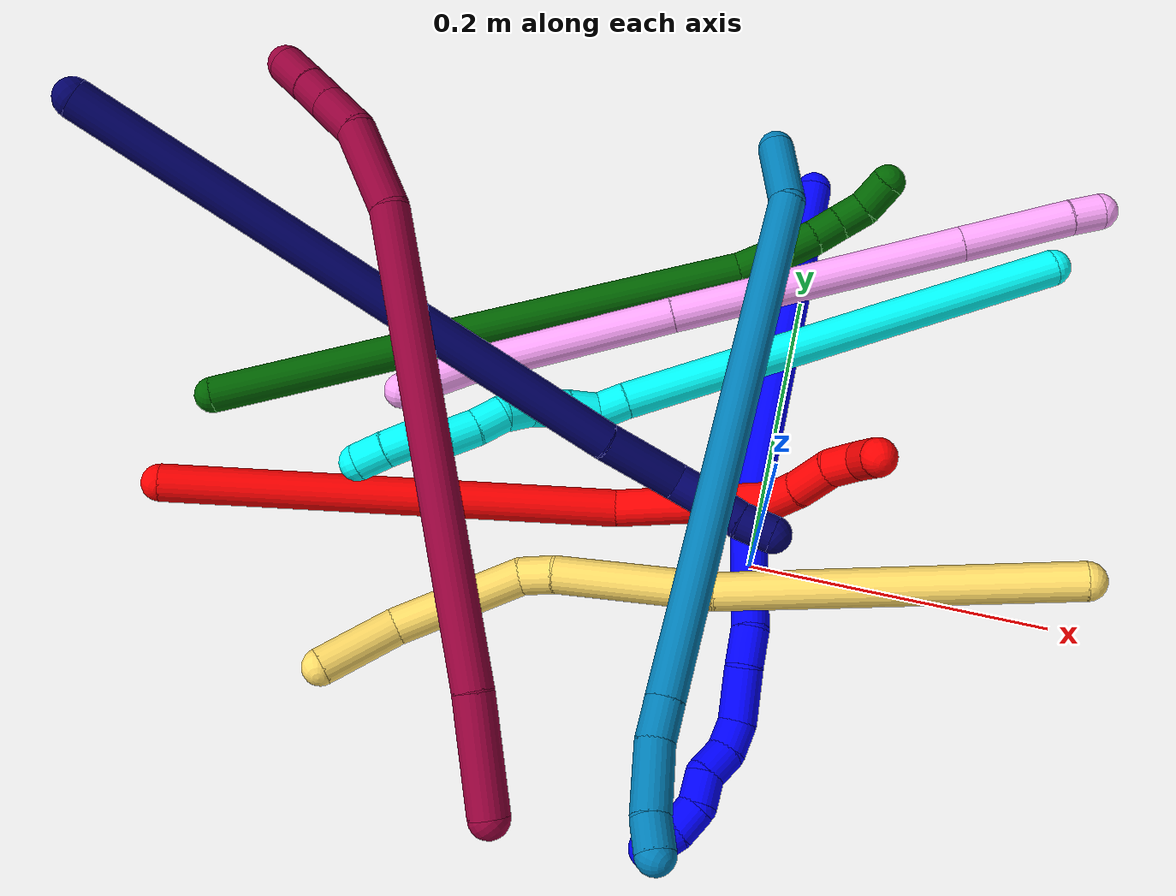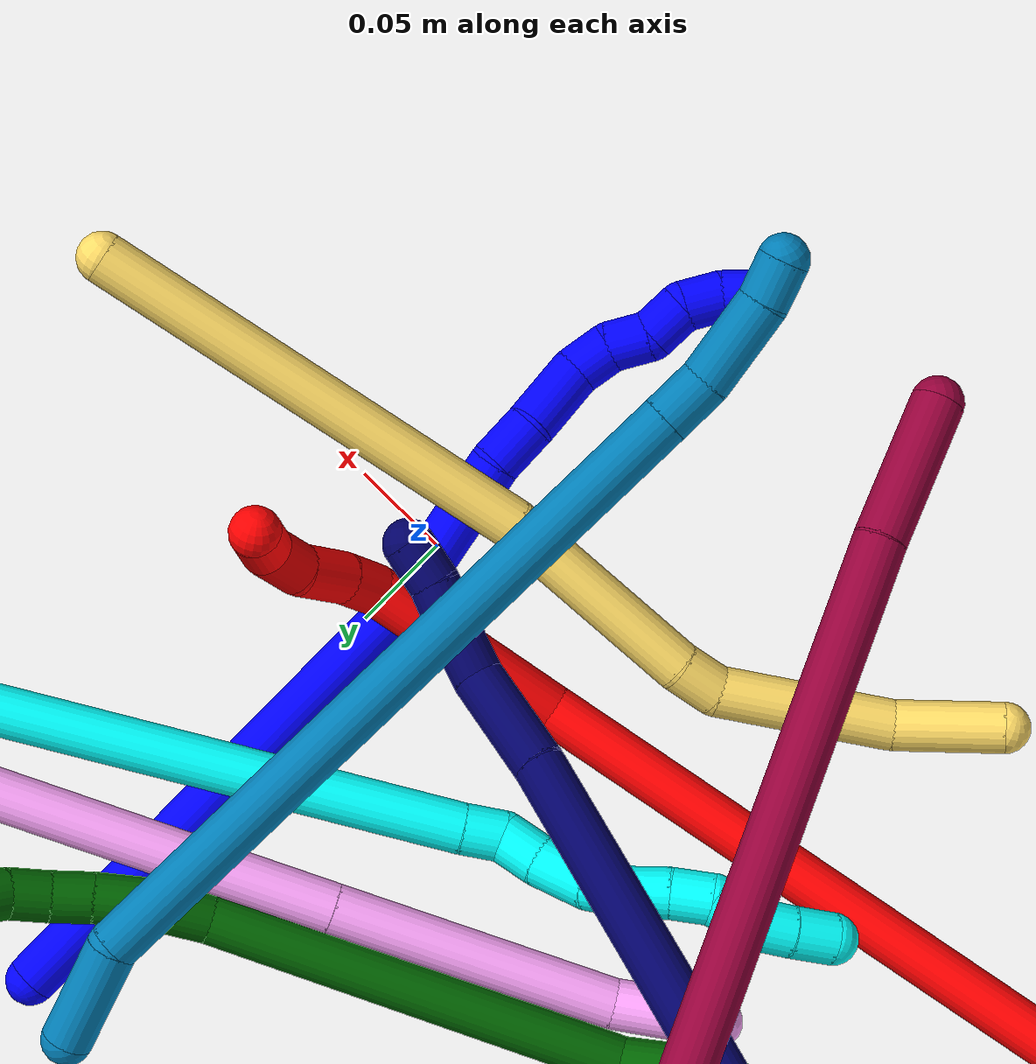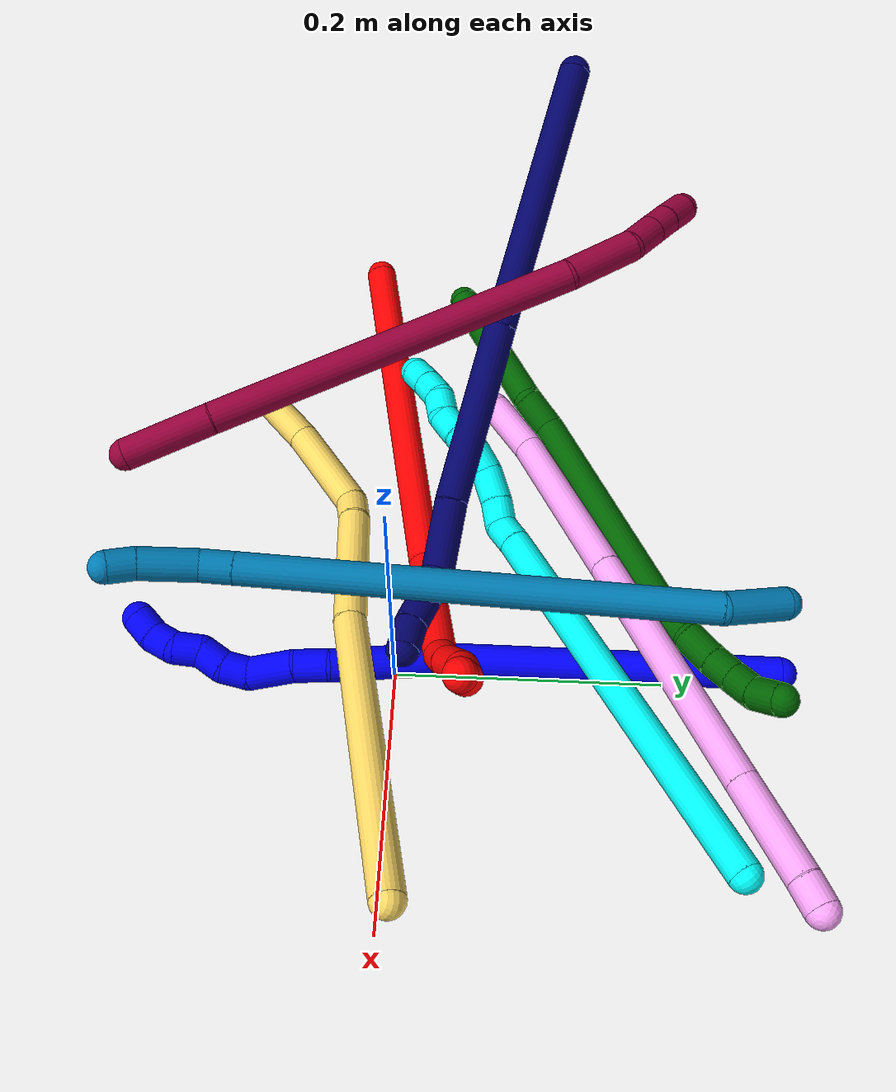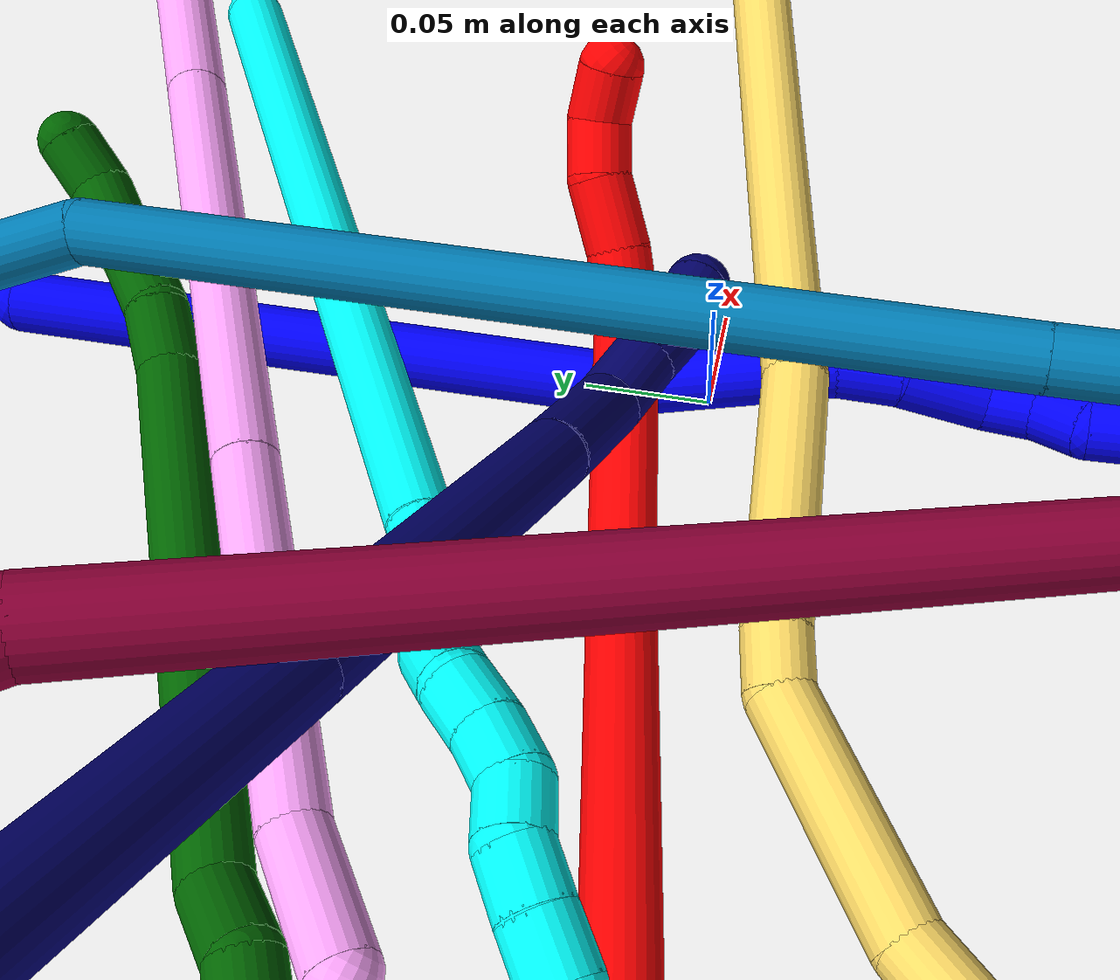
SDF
<sdf version="1.7">
 <world name="default">
  <plugin name="TubeGeneratorPlugin" filename="libtube_generator_plugin.so"/>
  <model name="photoneo_s_sensor">
   <static>1</static>
   <pose>0 0 2 1.57079 1.57079 3.14159</pose>
   <link name="link">
    <inertial><mass>0.1</mass></inertial>
    <sensor name="sensor" type="depth">
     <update_rate>30</update_rate>
     <camera>
      <horizontal_fov>1.22</horizontal_fov>
      <image><width>1920</width><height>1200</height><format>B8G8R8</format></image>
      <clip><near>0.1</near><far>4</far></clip>
      <depth_camera><output>points</output></depth_camera>
     </camera>
     <plugin name="camera_plugin" filename="libgazebo_ros_depth_camera.so">
      <baseline>0.2</baseline>
      <alwaysOn>1</alwaysOn>
      <updateRate>0.0</updateRate>
      <cameraName>camera_ir</cameraName>
      <imageTopicName>/camera/color/image_raw</imageTopicName>
      <cameraInfoTopicName>/camera/color/camera_info</cameraInfoTopicName>
      <depthImageTopicName>/camera/depth/image_raw</depthImageTopicName>
      <depthImageCameraInfoTopicName>/camera/depth/camera_info</depthImageCameraInfoTopicName>
      <pointCloudTopicName>/camera/depth/points</pointCloudTopicName>
      <frameName>fr_optical</frameName>
      <pointCloudCutoff>0.1</pointCloudCutoff>
      <pointCloudCutoffMax>2.0</pointCloudCutoffMax>
      <distortionK1>0</distortionK1>
      <distortionK2>0</distortionK2>
      <distortionK3>0</distortionK3>
      <distortionT1>0</distortionT1>
      <distortionT2>0</distortionT2>
      <CxPrime>0</CxPrime>
      <Cx>0</Cx>
      <Cy>0</Cy>
      <focalLength>0</focalLength>
      <hackBaseline>0</hackBaseline>
     </plugin>
    </sensor>
   </link>
  </model>
  <gravity>0 0 -9.8</gravity>
  <magnetic_field>6e-06 2.3e-05 -4.2e-05</magnetic_field>
  <atmosphere type="adiabatic"/>
  <physics name="default_physics" default="0" type="ode">
   <max_step_size>0.003</max_step_size>
   <real_time_factor>1</real_time_factor>
   <real_time_update_rate>1000</real_time_update_rate>
   <max_contacts>10000</max_contacts>
   <ode>
    <solver>
     <type>quick</type>
     <iters>100</iters>
     <sor>1.3</sor>
     <use_dynamic_moi_rescaling>0</use_dynamic_moi_rescaling>
    </solver>
    <constraints>
     <contact_max_correcting_vel>0</contact_max_correcting_vel>
     <contact_surface_layer>0.001</contact_surface_layer>
     <cfm>0</cfm>
     <erp>0.2</erp>
    </constraints>
   </ode>
  </physics>
  <scene><ambient>0.4 0.4 0.4 1</ambient><background>0.7 0.7 0.7 1</background><shadows>0</shadows></scene>
  <audio><device>default</device></audio>
  <spherical_coordinates>
   <surface_model>EARTH_WGS84</surface_model>
   <latitude_deg>0</latitude_deg>
   <longitude_deg>0</longitude_deg>
   <elevation>0</elevation>
   <heading_deg>0</heading_deg>
  </spherical_coordinates>
  <model name="bin">
   <static>1</static>
   <link name="bottom">
    <collision name="collision-bottom">
     <pose>0 0 -0.01 0 -0 0</pose>
     <geometry><box><size>0.8 0.6 0.02</size></box></geometry>
     <surface>
      <friction><ode><mu>100</mu><mu2>100</mu2></ode></friction>
      <contact><collide_bitmask>65535</collide_bitmask></contact>
     </surface>
    </collision>
   </link>
   <link name="west_wall">
    <collision name="collision-west_wall">
     <pose>-0.41 0 0.1 0 -0 0</pose>
     <geometry><box><size>0.02 0.6 0.2</size></box></geometry>
     <surface>
      <friction><ode><mu>100</mu><mu2>100</mu2></ode></friction>
      <contact><collide_bitmask>65535</collide_bitmask></contact>
     </surface>
    </collision>
   </link>
   <link name="east_wall">
    <collision name="collision-east_wall">
     <pose>0.41 0 0.1 0 -0 0</pose>
     <geometry><box><size>0.02 0.6 0.2</size></box></geometry>
     <surface>
      <friction><ode><mu>100</mu><mu2>100</mu2></ode></friction>
      <contact><collide_bitmask>65535</collide_bitmask></contact>
     </surface>
    </collision>
   </link>
   <link name="south_wall">
    <collision name="collision-south_wall">
     <pose>0 -0.31 0.1 0 -0 0</pose>
     <geometry><box><size>0.8 0.02 0.2</size></box></geometry>
     <surface>
      <friction><ode><mu>100</mu><mu2>100</mu2></ode></friction>
      <contact><collide_bitmask>65535</collide_bitmask></contact>
     </surface>
    </collision>
   </link>
   <link name="north_wall">
    <collision name="collision-north_wall">
     <pose>0 0.31 0.1 0 -0 0</pose>
     <geometry><box><size>0.8 0.02 0.2</size></box></geometry>
     <surface>
      <friction><ode><mu>100</mu><mu2>100</mu2></ode></friction>
      <contact><collide_bitmask>65535</collide_bitmask></contact>
     </surface>
    </collision>
   </link>
  </model>
  <model name="1">
   <static>0</static>
   <link name="1">
    <collision name="collision-cylinder-e_1_1_4">
     <pose>0.004167 -0.067378 -0.107217 2.58053 0.032893 0.114049</pose>
     <geometry><cylinder><radius>0.0125</radius><length>0.253397</length></cylinder></geometry>
     <surface>
      <friction><ode><mu>1.16</mu><mu2>1.16</mu2><slip1>0</slip1><slip2>0</slip2></ode></friction>
      <contact><ode><kp>1e+06</kp><kd>1</kd><max_vel>0</max_vel><min_depth>0.001</min_depth></ode></contact>
     </surface>
    </collision>
    <visual name="visual-cylinder-e_1_1_4">
     <pose>0.004167 -0.067378 -0.107217 2.58053 0.032893 0.114049</pose>
     <geometry><cylinder><radius>0.0125</radius><length>0.253397</length></cylinder></geometry>
     <material><ambient>0 0 1 1</ambient></material>
    </visual>
    <collision name="collision-cylinder-e_2_4_5">
     <pose>0.018001 -0.160297 -0.246495 2.46892 0.231609 0.642392</pose>
     <geometry><cylinder><radius>0.0125</radius><length>0.084232</length></cylinder></geometry>
     <surface>
      <friction><ode><mu>1.16</mu><mu2>1.16</mu2><slip1>0</slip1><slip2>0</slip2></ode></friction>
      <contact><ode><kp>1e+06</kp><kd>1</kd><max_vel>0</max_vel><min_depth>0.001</min_depth></ode></contact>
     </surface>
    </collision>
    <visual name="visual-cylinder-e_2_4_5">
     <pose>0.018001 -0.160297 -0.246495 2.46892 0.231609 0.642392</pose>
     <geometry><cylinder><radius>0.0125</radius><length>0.084232</length></cylinder></geometry>
     <material><ambient>0 0 1 1</ambient></material>
    </visual>
    <collision name="collision-cylinder-e_3_5_6">
     <pose>0.028412 -0.192003 -0.289494 2.62824 0.059161 0.224523</pose>
     <geometry><cylinder><radius>0.0125</radius><length>0.025153</length></cylinder></geometry>
     <surface>
      <friction><ode><mu>1.16</mu><mu2>1.16</mu2><slip1>0</slip1><slip2>0</slip2></ode></friction>
      <contact><ode><kp>1e+06</kp><kd>1</kd><max_vel>0</max_vel><min_depth>0.001</min_depth></ode></contact>
     </surface>
    </collision>
    <visual name="visual-cylinder-e_3_5_6">
     <pose>0.028412 -0.192003 -0.289494 2.62824 0.059161 0.224523</pose>
     <geometry><cylinder><radius>0.0125</radius><length>0.025153</length></cylinder></geometry>
     <material><ambient>0 0 1 1</ambient></material>
    </visual>
    <collision name="collision-cylinder-e_4_6_7">
     <pose>0.030727 -0.20312 -0.317366 2.85716 0.088833 0.601966</pose>
     <geometry><cylinder><radius>0.0125</radius><length>0.035429</length></cylinder></geometry>
     <surface>
      <friction><ode><mu>1.16</mu><mu2>1.16</mu2><slip1>0</slip1><slip2>0</slip2></ode></friction>
      <contact><ode><kp>1e+06</kp><kd>1</kd><max_vel>0</max_vel><min_depth>0.001</min_depth></ode></contact>
     </surface>
    </collision>
    <visual name="visual-cylinder-e_4_6_7">
     <pose>0.030727 -0.20312 -0.317366 2.85716 0.088833 0.601966</pose>
     <geometry><cylinder><radius>0.0125</radius><length>0.035429</length></cylinder></geometry>
     <material><ambient>0 0 1 1</ambient></material>
    </visual>
    <collision name="collision-cylinder-e_5_7_8">
     <pose>0.03093 -0.214476 -0.342249 2.46327 -0.133312 -0.374012</pose>
     <geometry><cylinder><radius>0.0125</radius><length>0.020597</length></cylinder></geometry>
     <surface>
      <friction><ode><mu>1.16</mu><mu2>1.16</mu2><slip1>0</slip1><slip2>0</slip2></ode></friction>
      <contact><ode><kp>1e+06</kp><kd>1</kd><max_vel>0</max_vel><min_depth>0.001</min_depth></ode></contact>
     </surface>
    </collision>
    <visual name="visual-cylinder-e_5_7_8">
     <pose>0.03093 -0.214476 -0.342249 2.46327 -0.133312 -0.374012</pose>
     <geometry><cylinder><radius>0.0125</radius><length>0.020597</length></cylinder></geometry>
     <material><ambient>0 0 1 1</ambient></material>
    </visual>
    <collision name="collision-cylinder-e_6_8_9">
     <pose>0.024914 -0.227658 -0.356329 2.30634 -0.470403 -0.990346</pose>
     <geometry><cylinder><radius>0.0125</radius><length>0.020509</length></cylinder></geometry>
     <surface>
      <friction><ode><mu>1.16</mu><mu2>1.16</mu2><slip1>0</slip1><slip2>0</slip2></ode></friction>
      <contact><ode><kp>1e+06</kp><kd>1</kd><max_vel>0</max_vel><min_depth>0.001</min_depth></ode></contact>
     </surface>
    </collision>
    <visual name="visual-cylinder-e_6_8_9">
     <pose>0.024914 -0.227658 -0.356329 2.30634 -0.470403 -0.990346</pose>
     <geometry><cylinder><radius>0.0125</radius><length>0.020509</length></cylinder></geometry>
     <material><ambient>0 0 1 1</ambient></material>
    </visual>
    <collision name="collision-cylinder-e_7_9_10">
     <pose>0.020239 -0.240724 -0.370632 2.48555 -0.002638 -0.007753</pose>
     <geometry><cylinder><radius>0.0125</radius><length>0.020618</length></cylinder></geometry>
     <surface>
      <friction><ode><mu>1.16</mu><mu2>1.16</mu2><slip1>0</slip1><slip2>0</slip2></ode></friction>
      <contact><ode><kp>1e+06</kp><kd>1</kd><max_vel>0</max_vel><min_depth>0.001</min_depth></ode></contact>
     </surface>
    </collision>
    <visual name="visual-cylinder-e_7_9_10">
     <pose>0.020239 -0.240724 -0.370632 2.48555 -0.002638 -0.007753</pose>
     <geometry><cylinder><radius>0.0125</radius><length>0.020618</length></cylinder></geometry>
     <material><ambient>0 0 1 1</ambient></material>
    </visual>
    <collision name="collision-cylinder-e_8_10_11">
     <pose>0.015441 -0.251416 -0.386434 2.61836 -0.496177 -1.51536</pose>
     <geometry><cylinder><radius>0.0125</radius><length>0.020039</length></cylinder></geometry>
     <surface>
      <friction><ode><mu>1.16</mu><mu2>1.16</mu2><slip1>0</slip1><slip2>0</slip2></ode></friction>
      <contact><ode><kp>1e+06</kp><kd>1</kd><max_vel>0</max_vel><min_depth>0.001</min_depth></ode></contact>
     </surface>
    </collision>
    <visual name="visual-cylinder-e_8_10_11">
     <pose>0.015441 -0.251416 -0.386434 2.61836 -0.496177 -1.51536</pose>
     <geometry><cylinder><radius>0.0125</radius><length>0.020039</length></cylinder></geometry>
     <material><ambient>0 0 1 1</ambient></material>
    </visual>
    <collision name="collision-cylinder-e_9_11_2">
     <pose>0.003942 -0.261248 -0.399113 2.31972 -0.737106 -1.45039</pose>
     <geometry><cylinder><radius>0.0125</radius><length>0.020025</length></cylinder></geometry>
     <surface>
      <friction><ode><mu>1.16</mu><mu2>1.16</mu2><slip1>0</slip1><slip2>0</slip2></ode></friction>
      <contact><ode><kp>1e+06</kp><kd>1</kd><max_vel>0</max_vel><min_depth>0.001</min_depth></ode></contact>
     </surface>
    </collision>
    <visual name="visual-cylinder-e_9_11_2">
     <pose>0.003942 -0.261248 -0.399113 2.31972 -0.737106 -1.45039</pose>
     <geometry><cylinder><radius>0.0125</radius><length>0.020025</length></cylinder></geometry>
     <material><ambient>0 0 1 1</ambient></material>
    </visual>
    <collision name="collision-sphere-2">
     <pose>-0.002788 -0.266678 -0.404161 0 -0 0</pose>
     <geometry><sphere><radius>0.0125</radius></sphere></geometry>
     <surface>
      <friction><ode><mu>1.16</mu><mu2>1.16</mu2><slip1>0</slip1><slip2>0</slip2></ode></friction>
      <contact><ode><kp>1e+06</kp><kd>1</kd><max_vel>0</max_vel><min_depth>0.001</min_depth></ode></contact>
     </surface>
    </collision>
    <visual name="visual-sphere-2">
     <pose>-0.002788 -0.266678 -0.404161 0 -0 0</pose>
     <geometry><sphere><radius>0.0125</radius></sphere></geometry>
     <material><ambient>0 0 1 1</ambient></material>
    </visual>
    <collision name="collision-sphere-11">
     <pose>0.010671 -0.255819 -0.394066 0 -0 0</pose>
     <geometry><sphere><radius>0.0125</radius></sphere></geometry>
     <surface>
      <friction><ode><mu>1.16</mu><mu2>1.16</mu2><slip1>0</slip1><slip2>0</slip2></ode></friction>
      <contact><ode><kp>1e+06</kp><kd>1</kd><max_vel>0</max_vel><min_depth>0.001</min_depth></ode></contact>
     </surface>
    </collision>
    <visual name="visual-sphere-11">
     <pose>0.010671 -0.255819 -0.394066 0 -0 0</pose>
     <geometry><sphere><radius>0.0125</radius></sphere></geometry>
     <material><ambient>0 0 1 1</ambient></material>
    </visual>
    <collision name="collision-sphere-10">
     <pose>0.020211 -0.247013 -0.378801 0 -0 0</pose>
     <geometry><sphere><radius>0.0125</radius></sphere></geometry>
     <surface>
      <friction><ode><mu>1.16</mu><mu2>1.16</mu2><slip1>0</slip1><slip2>0</slip2></ode></friction>
      <contact><ode><kp>1e+06</kp><kd>1</kd><max_vel>0</max_vel><min_depth>0.001</min_depth></ode></contact>
     </surface>
    </collision>
    <visual name="visual-sphere-10">
     <pose>0.020211 -0.247013 -0.378801 0 -0 0</pose>
     <geometry><sphere><radius>0.0125</radius></sphere></geometry>
     <material><ambient>0 0 1 1</ambient></material>
    </visual>
    <collision name="collision-sphere-9">
     <pose>0.020266 -0.234436 -0.362463 0 -0 0</pose>
     <geometry><sphere><radius>0.0125</radius></sphere></geometry>
     <surface>
      <friction><ode><mu>1.16</mu><mu2>1.16</mu2><slip1>0</slip1><slip2>0</slip2></ode></friction>
      <contact><ode><kp>1e+06</kp><kd>1</kd><max_vel>0</max_vel><min_depth>0.001</min_depth></ode></contact>
     </surface>
    </collision>
    <visual name="visual-sphere-9">
     <pose>0.020266 -0.234436 -0.362463 0 -0 0</pose>
     <geometry><sphere><radius>0.0125</radius></sphere></geometry>
     <material><ambient>0 0 1 1</ambient></material>
    </visual>
    <collision name="collision-sphere-4">
     <pose>0.008334 -0.134756 -0.214434 0 -0 0</pose>
     <geometry><sphere><radius>0.0125</radius></sphere></geometry>
     <surface>
      <friction><ode><mu>1.16</mu><mu2>1.16</mu2><slip1>0</slip1><slip2>0</slip2></ode></friction>
      <contact><ode><kp>1e+06</kp><kd>1</kd><max_vel>0</max_vel><min_depth>0.001</min_depth></ode></contact>
     </surface>
    </collision>
    <visual name="visual-sphere-4">
     <pose>0.008334 -0.134756 -0.214434 0 -0 0</pose>
     <geometry><sphere><radius>0.0125</radius></sphere></geometry>
     <material><ambient>0 0 1 1</ambient></material>
    </visual>
    <collision name="collision-sphere-1">
     <geometry><sphere><radius>0.0125</radius></sphere></geometry>
     <surface>
      <friction><ode><mu>1.16</mu><mu2>1.16</mu2><slip1>0</slip1><slip2>0</slip2></ode></friction>
      <contact><ode><kp>1e+06</kp><kd>1</kd><max_vel>0</max_vel><min_depth>0.001</min_depth></ode></contact>
     </surface>
    </collision>
    <visual name="visual-sphere-1">
     <geometry><sphere><radius>0.0125</radius></sphere></geometry>
     <material><ambient>0 0 1 1</ambient></material>
    </visual>
    <collision name="collision-sphere-8">
     <pose>0.029561 -0.220881 -0.350196 0 -0 0</pose>
     <geometry><sphere><radius>0.0125</radius></sphere></geometry>
     <surface>
      <friction><ode><mu>1.16</mu><mu2>1.16</mu2><slip1>0</slip1><slip2>0</slip2></ode></friction>
      <contact><ode><kp>1e+06</kp><kd>1</kd><max_vel>0</max_vel><min_depth>0.001</min_depth></ode></contact>
     </surface>
    </collision>
    <visual name="visual-sphere-8">
     <pose>0.029561 -0.220881 -0.350196 0 -0 0</pose>
     <geometry><sphere><radius>0.0125</radius></sphere></geometry>
     <material><ambient>0 0 1 1</ambient></material>
    </visual>
    <collision name="collision-sphere-5">
     <pose>0.027669 -0.185838 -0.278557 0 -0 0</pose>
     <geometry><sphere><radius>0.0125</radius></sphere></geometry>
     <surface>
      <friction><ode><mu>1.16</mu><mu2>1.16</mu2><slip1>0</slip1><slip2>0</slip2></ode></friction>
      <contact><ode><kp>1e+06</kp><kd>1</kd><max_vel>0</max_vel><min_depth>0.001</min_depth></ode></contact>
     </surface>
    </collision>
    <visual name="visual-sphere-5">
     <pose>0.027669 -0.185838 -0.278557 0 -0 0</pose>
     <geometry><sphere><radius>0.0125</radius></sphere></geometry>
     <material><ambient>0 0 1 1</ambient></material>
    </visual>
    <collision name="collision-sphere-6">
     <pose>0.029156 -0.198169 -0.30043 0 -0 0</pose>
     <geometry><sphere><radius>0.0125</radius></sphere></geometry>
     <surface>
      <friction><ode><mu>1.16</mu><mu2>1.16</mu2><slip1>0</slip1><slip2>0</slip2></ode></friction>
      <contact><ode><kp>1e+06</kp><kd>1</kd><max_vel>0</max_vel><min_depth>0.001</min_depth></ode></contact>
     </surface>
    </collision>
    <visual name="visual-sphere-6">
     <pose>0.029156 -0.198169 -0.30043 0 -0 0</pose>
     <geometry><sphere><radius>0.0125</radius></sphere></geometry>
     <material><ambient>0 0 1 1</ambient></material>
    </visual>
    <collision name="collision-sphere-7">
     <pose>0.032299 -0.208071 -0.334301 0 -0 0</pose>
     <geometry><sphere><radius>0.0125</radius></sphere></geometry>
     <surface>
      <friction><ode><mu>1.16</mu><mu2>1.16</mu2><slip1>0</slip1><slip2>0</slip2></ode></friction>
      <contact><ode><kp>1e+06</kp><kd>1</kd><max_vel>0</max_vel><min_depth>0.001</min_depth></ode></contact>
     </surface>
    </collision>
    <visual name="visual-sphere-7">
     <pose>0.032299 -0.208071 -0.334301 0 -0 0</pose>
     <geometry><sphere><radius>0.0125</radius></sphere></geometry>
     <material><ambient>0 0 1 1</ambient></material>
    </visual>
    <inertial>
     <pose>0.012658 -0.133842 -0.208384 0 -0 0</pose>
     <mass>0.5</mass>
     <inertia>
      <ixx>0.001593</ixx>
      <ixy>0</ixy>
      <ixz>0</ixz>
      <iyy>-0.001018</iyy>
      <iyz>0</iyz>
      <izz>0.000679</izz>
     </inertia>
    </inertial>
   </link>
   <pose>-0.007295 0.287455 0.011496 -1.00795 -0.091675 -0.034552</pose>
  </model>
  <model name="2">
   <static>0</static>
   <link name="2">
    <collision name="collision-cylinder-e_1_1_4">
     <pose>0.146229 0.02123 -0.027482 -2.48385 1.33763 -2.32636</pose>
     <geometry><cylinder><radius>0.0125</radius><length>0.300592</length></cylinder></geometry>
     <surface>
      <friction><ode><mu>1.16</mu><mu2>1.16</mu2><slip1>0</slip1><slip2>0</slip2></ode></friction>
      <contact><ode><kp>1e+06</kp><kd>1</kd><max_vel>0</max_vel><min_depth>0.001</min_depth></ode></contact>
     </surface>
    </collision>
    <visual name="visual-cylinder-e_1_1_4">
     <pose>0.146229 0.02123 -0.027482 -2.48385 1.33763 -2.32636</pose>
     <geometry><cylinder><radius>0.0125</radius><length>0.300592</length></cylinder></geometry>
     <material><ambient>1 0 0 1</ambient></material>
    </visual>
    <collision name="collision-cylinder-e_2_4_5">
     <pose>0.339623 0.036436 -0.078152 2.88744 1.10081 2.73106</pose>
     <geometry><cylinder><radius>0.0125</radius><length>0.105803</length></cylinder></geometry>
     <surface>
      <friction><ode><mu>1.16</mu><mu2>1.16</mu2><slip1>0</slip1><slip2>0</slip2></ode></friction>
      <contact><ode><kp>1e+06</kp><kd>1</kd><max_vel>0</max_vel><min_depth>0.001</min_depth></ode></contact>
     </surface>
    </collision>
    <visual name="visual-cylinder-e_2_4_5">
     <pose>0.339623 0.036436 -0.078152 2.88744 1.10081 2.73106</pose>
     <geometry><cylinder><radius>0.0125</radius><length>0.105803</length></cylinder></geometry>
     <material><ambient>1 0 0 1</ambient></material>
    </visual>
    <collision name="collision-cylinder-e_3_5_6">
     <pose>0.393759 0.024381 -0.107429 2.36093 0.682768 1.4246</pose>
     <geometry><cylinder><radius>0.0125</radius><length>0.022094</length></cylinder></geometry>
     <surface>
      <friction><ode><mu>1.16</mu><mu2>1.16</mu2><slip1>0</slip1><slip2>0</slip2></ode></friction>
      <contact><ode><kp>1e+06</kp><kd>1</kd><max_vel>0</max_vel><min_depth>0.001</min_depth></ode></contact>
     </surface>
    </collision>
    <visual name="visual-cylinder-e_3_5_6">
     <pose>0.393759 0.024381 -0.107429 2.36093 0.682768 1.4246</pose>
     <geometry><cylinder><radius>0.0125</radius><length>0.022094</length></cylinder></geometry>
     <material><ambient>1 0 0 1</ambient></material>
    </visual>
    <collision name="collision-cylinder-e_4_6_7">
     <pose>0.409081 0.009096 -0.120306 2.20373 0.629165 1.14184</pose>
     <geometry><cylinder><radius>0.0125</radius><length>0.028386</length></cylinder></geometry>
     <surface>
      <friction><ode><mu>1.16</mu><mu2>1.16</mu2><slip1>0</slip1><slip2>0</slip2></ode></friction>
      <contact><ode><kp>1e+06</kp><kd>1</kd><max_vel>0</max_vel><min_depth>0.001</min_depth></ode></contact>
     </surface>
    </collision>
    <visual name="visual-cylinder-e_4_6_7">
     <pose>0.409081 0.009096 -0.120306 2.20373 0.629165 1.14184</pose>
     <geometry><cylinder><radius>0.0125</radius><length>0.028386</length></cylinder></geometry>
     <material><ambient>1 0 0 1</ambient></material>
    </visual>
    <collision name="collision-cylinder-e_5_7_8">
     <pose>0.424549 -0.004786 -0.134119 2.5589 0.701964 1.76911</pose>
     <geometry><cylinder><radius>0.0125</radius><length>0.022039</length></cylinder></geometry>
     <surface>
      <friction><ode><mu>1.16</mu><mu2>1.16</mu2><slip1>0</slip1><slip2>0</slip2></ode></friction>
      <contact><ode><kp>1e+06</kp><kd>1</kd><max_vel>0</max_vel><min_depth>0.001</min_depth></ode></contact>
     </surface>
    </collision>
    <visual name="visual-cylinder-e_5_7_8">
     <pose>0.424549 -0.004786 -0.134119 2.5589 0.701964 1.76911</pose>
     <geometry><cylinder><radius>0.0125</radius><length>0.022039</length></cylinder></geometry>
     <material><ambient>1 0 0 1</ambient></material>
    </visual>
    <collision name="collision-cylinder-e_6_8_2">
     <pose>0.433682 -0.014312 -0.150262 2.64879 0.19258 0.733326</pose>
     <geometry><cylinder><radius>0.0125</radius><length>0.021087</length></cylinder></geometry>
     <surface>
      <friction><ode><mu>1.16</mu><mu2>1.16</mu2><slip1>0</slip1><slip2>0</slip2></ode></friction>
      <contact><ode><kp>1e+06</kp><kd>1</kd><max_vel>0</max_vel><min_depth>0.001</min_depth></ode></contact>
     </surface>
    </collision>
    <visual name="visual-cylinder-e_6_8_2">
     <pose>0.433682 -0.014312 -0.150262 2.64879 0.19258 0.733326</pose>
     <geometry><cylinder><radius>0.0125</radius><length>0.021087</length></cylinder></geometry>
     <material><ambient>1 0 0 1</ambient></material>
    </visual>
    <collision name="collision-sphere-2">
     <pose>0.4357 -0.019208 -0.159379 0 -0 0</pose>
     <geometry><sphere><radius>0.0125</radius></sphere></geometry>
     <surface>
      <friction><ode><mu>1.16</mu><mu2>1.16</mu2><slip1>0</slip1><slip2>0</slip2></ode></friction>
      <contact><ode><kp>1e+06</kp><kd>1</kd><max_vel>0</max_vel><min_depth>0.001</min_depth></ode></contact>
     </surface>
    </collision>
    <visual name="visual-sphere-2">
     <pose>0.4357 -0.019208 -0.159379 0 -0 0</pose>
     <geometry><sphere><radius>0.0125</radius></sphere></geometry>
     <material><ambient>1 0 0 1</ambient></material>
    </visual>
    <collision name="collision-sphere-4">
     <pose>0.292458 0.042459 -0.054964 0 -0 0</pose>
     <geometry><sphere><radius>0.0125</radius></sphere></geometry>
     <surface>
      <friction><ode><mu>1.16</mu><mu2>1.16</mu2><slip1>0</slip1><slip2>0</slip2></ode></friction>
      <contact><ode><kp>1e+06</kp><kd>1</kd><max_vel>0</max_vel><min_depth>0.001</min_depth></ode></contact>
     </surface>
    </collision>
    <visual name="visual-sphere-4">
     <pose>0.292458 0.042459 -0.054964 0 -0 0</pose>
     <geometry><sphere><radius>0.0125</radius></sphere></geometry>
     <material><ambient>1 0 0 1</ambient></material>
    </visual>
    <collision name="collision-sphere-1">
     <geometry><sphere><radius>0.0125</radius></sphere></geometry>
     <surface>
      <friction><ode><mu>1.16</mu><mu2>1.16</mu2><slip1>0</slip1><slip2>0</slip2></ode></friction>
      <contact><ode><kp>1e+06</kp><kd>1</kd><max_vel>0</max_vel><min_depth>0.001</min_depth></ode></contact>
     </surface>
    </collision>
    <visual name="visual-sphere-1">
     <geometry><sphere><radius>0.0125</radius></sphere></geometry>
     <material><ambient>1 0 0 1</ambient></material>
    </visual>
    <collision name="collision-sphere-8">
     <pose>0.431664 -0.009416 -0.141145 0 -0 0</pose>
     <geometry><sphere><radius>0.0125</radius></sphere></geometry>
     <surface>
      <friction><ode><mu>1.16</mu><mu2>1.16</mu2><slip1>0</slip1><slip2>0</slip2></ode></friction>
      <contact><ode><kp>1e+06</kp><kd>1</kd><max_vel>0</max_vel><min_depth>0.001</min_depth></ode></contact>
     </surface>
    </collision>
    <visual name="visual-sphere-8">
     <pose>0.431664 -0.009416 -0.141145 0 -0 0</pose>
     <geometry><sphere><radius>0.0125</radius></sphere></geometry>
     <material><ambient>1 0 0 1</ambient></material>
    </visual>
    <collision name="collision-sphere-5">
     <pose>0.386789 0.030412 -0.10134 0 -0 0</pose>
     <geometry><sphere><radius>0.0125</radius></sphere></geometry>
     <surface>
      <friction><ode><mu>1.16</mu><mu2>1.16</mu2><slip1>0</slip1><slip2>0</slip2></ode></friction>
      <contact><ode><kp>1e+06</kp><kd>1</kd><max_vel>0</max_vel><min_depth>0.001</min_depth></ode></contact>
     </surface>
    </collision>
    <visual name="visual-sphere-5">
     <pose>0.386789 0.030412 -0.10134 0 -0 0</pose>
     <geometry><sphere><radius>0.0125</radius></sphere></geometry>
     <material><ambient>1 0 0 1</ambient></material>
    </visual>
    <collision name="collision-sphere-6">
     <pose>0.400729 0.018349 -0.113518 0 -0 0</pose>
     <geometry><sphere><radius>0.0125</radius></sphere></geometry>
     <surface>
      <friction><ode><mu>1.16</mu><mu2>1.16</mu2><slip1>0</slip1><slip2>0</slip2></ode></friction>
      <contact><ode><kp>1e+06</kp><kd>1</kd><max_vel>0</max_vel><min_depth>0.001</min_depth></ode></contact>
     </surface>
    </collision>
    <visual name="visual-sphere-6">
     <pose>0.400729 0.018349 -0.113518 0 -0 0</pose>
     <geometry><sphere><radius>0.0125</radius></sphere></geometry>
     <material><ambient>1 0 0 1</ambient></material>
    </visual>
    <collision name="collision-sphere-7">
     <pose>0.417433 -0.000156 -0.127094 0 -0 0</pose>
     <geometry><sphere><radius>0.0125</radius></sphere></geometry>
     <surface>
      <friction><ode><mu>1.16</mu><mu2>1.16</mu2><slip1>0</slip1><slip2>0</slip2></ode></friction>
      <contact><ode><kp>1e+06</kp><kd>1</kd><max_vel>0</max_vel><min_depth>0.001</min_depth></ode></contact>
     </surface>
    </collision>
    <visual name="visual-sphere-7">
     <pose>0.417433 -0.000156 -0.127094 0 -0 0</pose>
     <geometry><sphere><radius>0.0125</radius></sphere></geometry>
     <material><ambient>1 0 0 1</ambient></material>
    </visual>
    <inertial>
     <pose>0.237403 0.021252 -0.056885 0 -0 0</pose>
     <mass>0.5</mass>
     <inertia>
      <ixx>-0.000725</ixx>
      <ixy>0</ixy>
      <ixz>0</ixz>
      <iyy>0.001961</iyy>
      <iyz>0</iyz>
      <izz>-0.002627</izz>
     </inertia>
    </inertial>
   </link>
   <pose>-0.388506 -0.038365 0.04103 -2.33399 0.124027 0.420526</pose>
  </model>
  <model name="3">
   <static>0</static>
   <link name="3">
    <collision name="collision-cylinder-e_1_1_4">
     <pose>-0.126585 -0.088237 -0.010183 1.68569 -0.95894 -1.05623</pose>
     <geometry><cylinder><radius>0.0125</radius><length>0.309278</length></cylinder></geometry>
     <surface>
      <friction><ode><mu>1.16</mu><mu2>1.16</mu2><slip1>0</slip1><slip2>0</slip2></ode></friction>
      <contact><ode><kp>1e+06</kp><kd>1</kd><max_vel>0</max_vel><min_depth>0.001</min_depth></ode></contact>
     </surface>
    </collision>
    <visual name="visual-cylinder-e_1_1_4">
     <pose>-0.126585 -0.088237 -0.010183 1.68569 -0.95894 -1.05623</pose>
     <geometry><cylinder><radius>0.0125</radius><length>0.309278</length></cylinder></geometry>
     <material><ambient>0.003922 1 0.996078 1</ambient></material>
    </visual>
    <collision name="collision-cylinder-e_2_4_5">
     <pose>-0.261404 -0.182318 -0.020367 1.57097 -0.953597 -0.953735</pose>
     <geometry><cylinder><radius>0.0125</radius><length>0.020196</length></cylinder></geometry>
     <surface>
      <friction><ode><mu>1.16</mu><mu2>1.16</mu2><slip1>0</slip1><slip2>0</slip2></ode></friction>
      <contact><ode><kp>1e+06</kp><kd>1</kd><max_vel>0</max_vel><min_depth>0.001</min_depth></ode></contact>
     </surface>
    </collision>
    <visual name="visual-cylinder-e_2_4_5">
     <pose>-0.261404 -0.182318 -0.020367 1.57097 -0.953597 -0.953735</pose>
     <geometry><cylinder><radius>0.0125</radius><length>0.020196</length></cylinder></geometry>
     <material><ambient>0.003922 1 0.996078 1</ambient></material>
    </visual>
    <collision name="collision-cylinder-e_3_5_6">
     <pose>-0.278334 -0.191913 -0.025065 2.46781 -0.965912 -1.96384</pose>
     <geometry><cylinder><radius>0.0125</radius><length>0.021141</length></cylinder></geometry>
     <surface>
      <friction><ode><mu>1.16</mu><mu2>1.16</mu2><slip1>0</slip1><slip2>0</slip2></ode></friction>
      <contact><ode><kp>1e+06</kp><kd>1</kd><max_vel>0</max_vel><min_depth>0.001</min_depth></ode></contact>
     </surface>
    </collision>
    <visual name="visual-cylinder-e_3_5_6">
     <pose>-0.278334 -0.191913 -0.025065 2.46781 -0.965912 -1.96384</pose>
     <geometry><cylinder><radius>0.0125</radius><length>0.021141</length></cylinder></geometry>
     <material><ambient>0.003922 1 0.996078 1</ambient></material>
    </visual>
    <collision name="collision-cylinder-e_4_6_7">
     <pose>-0.299086 -0.199401 -0.034079 2.42794 -1.12857 -2.07704</pose>
     <geometry><cylinder><radius>0.0125</radius><length>0.026682</length></cylinder></geometry>
     <surface>
      <friction><ode><mu>1.16</mu><mu2>1.16</mu2><slip1>0</slip1><slip2>0</slip2></ode></friction>
      <contact><ode><kp>1e+06</kp><kd>1</kd><max_vel>0</max_vel><min_depth>0.001</min_depth></ode></contact>
     </surface>
    </collision>
    <visual name="visual-cylinder-e_4_6_7">
     <pose>-0.299086 -0.199401 -0.034079 2.42794 -1.12857 -2.07704</pose>
     <geometry><cylinder><radius>0.0125</radius><length>0.026682</length></cylinder></geometry>
     <material><ambient>0.003922 1 0.996078 1</ambient></material>
    </visual>
    <collision name="collision-cylinder-e_5_7_8">
     <pose>-0.321155 -0.204268 -0.039656 2.41134 -1.40322 -2.29196</pose>
     <geometry><cylinder><radius>0.0125</radius><length>0.020307</length></cylinder></geometry>
     <surface>
      <friction><ode><mu>1.16</mu><mu2>1.16</mu2><slip1>0</slip1><slip2>0</slip2></ode></friction>
      <contact><ode><kp>1e+06</kp><kd>1</kd><max_vel>0</max_vel><min_depth>0.001</min_depth></ode></contact>
     </surface>
    </collision>
    <visual name="visual-cylinder-e_5_7_8">
     <pose>-0.321155 -0.204268 -0.039656 2.41134 -1.40322 -2.29196</pose>
     <geometry><cylinder><radius>0.0125</radius><length>0.020307</length></cylinder></geometry>
     <material><ambient>0.003922 1 0.996078 1</ambient></material>
    </visual>
    <collision name="collision-cylinder-e_6_8_9">
     <pose>-0.340481 -0.209447 -0.039749 1.2898 -1.14594 -0.90362</pose>
     <geometry><cylinder><radius>0.0125</radius><length>0.020447</length></cylinder></geometry>
     <surface>
      <friction><ode><mu>1.16</mu><mu2>1.16</mu2><slip1>0</slip1><slip2>0</slip2></ode></friction>
      <contact><ode><kp>1e+06</kp><kd>1</kd><max_vel>0</max_vel><min_depth>0.001</min_depth></ode></contact>
     </surface>
    </collision>
    <visual name="visual-cylinder-e_6_8_9">
     <pose>-0.340481 -0.209447 -0.039749 1.2898 -1.14594 -0.90362</pose>
     <geometry><cylinder><radius>0.0125</radius><length>0.020447</length></cylinder></geometry>
     <material><ambient>0.003922 1 0.996078 1</ambient></material>
    </visual>
    <collision name="collision-cylinder-e_7_9_10">
     <pose>-0.359072 -0.217723 -0.038605 1.57654 -1.14317 -1.1484</pose>
     <geometry><cylinder><radius>0.0125</radius><length>0.020389</length></cylinder></geometry>
     <surface>
      <friction><ode><mu>1.16</mu><mu2>1.16</mu2><slip1>0</slip1><slip2>0</slip2></ode></friction>
      <contact><ode><kp>1e+06</kp><kd>1</kd><max_vel>0</max_vel><min_depth>0.001</min_depth></ode></contact>
     </surface>
    </collision>
    <visual name="visual-cylinder-e_7_9_10">
     <pose>-0.359072 -0.217723 -0.038605 1.57654 -1.14317 -1.1484</pose>
     <geometry><cylinder><radius>0.0125</radius><length>0.020389</length></cylinder></geometry>
     <material><ambient>0.003922 1 0.996078 1</ambient></material>
    </visual>
    <collision name="collision-cylinder-e_8_10_11">
     <pose>-0.375935 -0.227396 -0.042499 2.18865 -0.848776 -1.43817</pose>
     <geometry><cylinder><radius>0.0125</radius><length>0.020216</length></cylinder></geometry>
     <surface>
      <friction><ode><mu>1.16</mu><mu2>1.16</mu2><slip1>0</slip1><slip2>0</slip2></ode></friction>
      <contact><ode><kp>1e+06</kp><kd>1</kd><max_vel>0</max_vel><min_depth>0.001</min_depth></ode></contact>
     </surface>
    </collision>
    <visual name="visual-cylinder-e_8_10_11">
     <pose>-0.375935 -0.227396 -0.042499 2.18865 -0.848776 -1.43817</pose>
     <geometry><cylinder><radius>0.0125</radius><length>0.020216</length></cylinder></geometry>
     <material><ambient>0.003922 1 0.996078 1</ambient></material>
    </visual>
    <collision name="collision-cylinder-e_9_11_12">
     <pose>-0.391106 -0.239638 -0.04636 1.56949 -0.840185 -0.839211</pose>
     <geometry><cylinder><radius>0.0125</radius><length>0.020368</length></cylinder></geometry>
     <surface>
      <friction><ode><mu>1.16</mu><mu2>1.16</mu2><slip1>0</slip1><slip2>0</slip2></ode></friction>
      <contact><ode><kp>1e+06</kp><kd>1</kd><max_vel>0</max_vel><min_depth>0.001</min_depth></ode></contact>
     </surface>
    </collision>
    <visual name="visual-cylinder-e_9_11_12">
     <pose>-0.391106 -0.239638 -0.04636 1.56949 -0.840185 -0.839211</pose>
     <geometry><cylinder><radius>0.0125</radius><length>0.020368</length></cylinder></geometry>
     <material><ambient>0.003922 1 0.996078 1</ambient></material>
    </visual>
    <collision name="collision-cylinder-e_10_12_2">
     <pose>-0.406252 -0.25368 -0.045796 1.49425 -0.805209 -0.751433</pose>
     <geometry><cylinder><radius>0.0125</radius><length>0.020976</length></cylinder></geometry>
     <surface>
      <friction><ode><mu>1.16</mu><mu2>1.16</mu2><slip1>0</slip1><slip2>0</slip2></ode></friction>
      <contact><ode><kp>1e+06</kp><kd>1</kd><max_vel>0</max_vel><min_depth>0.001</min_depth></ode></contact>
     </surface>
    </collision>
    <visual name="visual-cylinder-e_10_12_2">
     <pose>-0.406252 -0.25368 -0.045796 1.49425 -0.805209 -0.751433</pose>
     <geometry><cylinder><radius>0.0125</radius><length>0.020976</length></cylinder></geometry>
     <material><ambient>0.003922 1 0.996078 1</ambient></material>
    </visual>
    <collision name="collision-sphere-2">
     <pose>-0.413814 -0.260927 -0.04524 0 -0 0</pose>
     <geometry><sphere><radius>0.0125</radius></sphere></geometry>
     <surface>
      <friction><ode><mu>1.16</mu><mu2>1.16</mu2><slip1>0</slip1><slip2>0</slip2></ode></friction>
      <contact><ode><kp>1e+06</kp><kd>1</kd><max_vel>0</max_vel><min_depth>0.001</min_depth></ode></contact>
     </surface>
    </collision>
    <visual name="visual-sphere-2">
     <pose>-0.413814 -0.260927 -0.04524 0 -0 0</pose>
     <geometry><sphere><radius>0.0125</radius></sphere></geometry>
     <material><ambient>0.003922 1 0.996078 1</ambient></material>
    </visual>
    <collision name="collision-sphere-12">
     <pose>-0.398691 -0.246434 -0.046352 0 -0 0</pose>
     <geometry><sphere><radius>0.0125</radius></sphere></geometry>
     <surface>
      <friction><ode><mu>1.16</mu><mu2>1.16</mu2><slip1>0</slip1><slip2>0</slip2></ode></friction>
      <contact><ode><kp>1e+06</kp><kd>1</kd><max_vel>0</max_vel><min_depth>0.001</min_depth></ode></contact>
     </surface>
    </collision>
    <visual name="visual-sphere-12">
     <pose>-0.398691 -0.246434 -0.046352 0 -0 0</pose>
     <geometry><sphere><radius>0.0125</radius></sphere></geometry>
     <material><ambient>0.003922 1 0.996078 1</ambient></material>
    </visual>
    <collision name="collision-sphere-11">
     <pose>-0.383521 -0.232842 -0.046369 0 -0 0</pose>
     <geometry><sphere><radius>0.0125</radius></sphere></geometry>
     <surface>
      <friction><ode><mu>1.16</mu><mu2>1.16</mu2><slip1>0</slip1><slip2>0</slip2></ode></friction>
      <contact><ode><kp>1e+06</kp><kd>1</kd><max_vel>0</max_vel><min_depth>0.001</min_depth></ode></contact>
     </surface>
    </collision>
    <visual name="visual-sphere-11">
     <pose>-0.383521 -0.232842 -0.046369 0 -0 0</pose>
     <geometry><sphere><radius>0.0125</radius></sphere></geometry>
     <material><ambient>0.003922 1 0.996078 1</ambient></material>
    </visual>
    <collision name="collision-sphere-10">
     <pose>-0.368349 -0.221951 -0.038629 0 -0 0</pose>
     <geometry><sphere><radius>0.0125</radius></sphere></geometry>
     <surface>
      <friction><ode><mu>1.16</mu><mu2>1.16</mu2><slip1>0</slip1><slip2>0</slip2></ode></friction>
      <contact><ode><kp>1e+06</kp><kd>1</kd><max_vel>0</max_vel><min_depth>0.001</min_depth></ode></contact>
     </surface>
    </collision>
    <visual name="visual-sphere-10">
     <pose>-0.368349 -0.221951 -0.038629 0 -0 0</pose>
     <geometry><sphere><radius>0.0125</radius></sphere></geometry>
     <material><ambient>0.003922 1 0.996078 1</ambient></material>
    </visual>
    <collision name="collision-sphere-9">
     <pose>-0.349796 -0.213495 -0.038581 0 -0 0</pose>
     <geometry><sphere><radius>0.0125</radius></sphere></geometry>
     <surface>
      <friction><ode><mu>1.16</mu><mu2>1.16</mu2><slip1>0</slip1><slip2>0</slip2></ode></friction>
      <contact><ode><kp>1e+06</kp><kd>1</kd><max_vel>0</max_vel><min_depth>0.001</min_depth></ode></contact>
     </surface>
    </collision>
    <visual name="visual-sphere-9">
     <pose>-0.349796 -0.213495 -0.038581 0 -0 0</pose>
     <geometry><sphere><radius>0.0125</radius></sphere></geometry>
     <material><ambient>0.003922 1 0.996078 1</ambient></material>
    </visual>
    <collision name="collision-sphere-4">
     <pose>-0.253169 -0.176474 -0.020366 0 -0 0</pose>
     <geometry><sphere><radius>0.0125</radius></sphere></geometry>
     <surface>
      <friction><ode><mu>1.16</mu><mu2>1.16</mu2><slip1>0</slip1><slip2>0</slip2></ode></friction>
      <contact><ode><kp>1e+06</kp><kd>1</kd><max_vel>0</max_vel><min_depth>0.001</min_depth></ode></contact>
     </surface>
    </collision>
    <visual name="visual-sphere-4">
     <pose>-0.253169 -0.176474 -0.020366 0 -0 0</pose>
     <geometry><sphere><radius>0.0125</radius></sphere></geometry>
     <material><ambient>0.003922 1 0.996078 1</ambient></material>
    </visual>
    <collision name="collision-sphere-1">
     <geometry><sphere><radius>0.0125</radius></sphere></geometry>
     <surface>
      <friction><ode><mu>1.16</mu><mu2>1.16</mu2><slip1>0</slip1><slip2>0</slip2></ode></friction>
      <contact><ode><kp>1e+06</kp><kd>1</kd><max_vel>0</max_vel><min_depth>0.001</min_depth></ode></contact>
     </surface>
    </collision>
    <visual name="visual-sphere-1">
     <geometry><sphere><radius>0.0125</radius></sphere></geometry>
     <material><ambient>0.003922 1 0.996078 1</ambient></material>
    </visual>
    <collision name="collision-sphere-8">
     <pose>-0.331167 -0.205398 -0.040918 0 -0 0</pose>
     <geometry><sphere><radius>0.0125</radius></sphere></geometry>
     <surface>
      <friction><ode><mu>1.16</mu><mu2>1.16</mu2><slip1>0</slip1><slip2>0</slip2></ode></friction>
      <contact><ode><kp>1e+06</kp><kd>1</kd><max_vel>0</max_vel><min_depth>0.001</min_depth></ode></contact>
     </surface>
    </collision>
    <visual name="visual-sphere-8">
     <pose>-0.331167 -0.205398 -0.040918 0 -0 0</pose>
     <geometry><sphere><radius>0.0125</radius></sphere></geometry>
     <material><ambient>0.003922 1 0.996078 1</ambient></material>
    </visual>
    <collision name="collision-sphere-5">
     <pose>-0.269639 -0.188163 -0.020368 0 -0 0</pose>
     <geometry><sphere><radius>0.0125</radius></sphere></geometry>
     <surface>
      <friction><ode><mu>1.16</mu><mu2>1.16</mu2><slip1>0</slip1><slip2>0</slip2></ode></friction>
      <contact><ode><kp>1e+06</kp><kd>1</kd><max_vel>0</max_vel><min_depth>0.001</min_depth></ode></contact>
     </surface>
    </collision>
    <visual name="visual-sphere-5">
     <pose>-0.269639 -0.188163 -0.020368 0 -0 0</pose>
     <geometry><sphere><radius>0.0125</radius></sphere></geometry>
     <material><ambient>0.003922 1 0.996078 1</ambient></material>
    </visual>
    <collision name="collision-sphere-6">
     <pose>-0.287029 -0.195664 -0.029763 0 -0 0</pose>
     <geometry><sphere><radius>0.0125</radius></sphere></geometry>
     <surface>
      <friction><ode><mu>1.16</mu><mu2>1.16</mu2><slip1>0</slip1><slip2>0</slip2></ode></friction>
      <contact><ode><kp>1e+06</kp><kd>1</kd><max_vel>0</max_vel><min_depth>0.001</min_depth></ode></contact>
     </surface>
    </collision>
    <visual name="visual-sphere-6">
     <pose>-0.287029 -0.195664 -0.029763 0 -0 0</pose>
     <geometry><sphere><radius>0.0125</radius></sphere></geometry>
     <material><ambient>0.003922 1 0.996078 1</ambient></material>
    </visual>
    <collision name="collision-sphere-7">
     <pose>-0.311144 -0.203138 -0.038395 0 -0 0</pose>
     <geometry><sphere><radius>0.0125</radius></sphere></geometry>
     <surface>
      <friction><ode><mu>1.16</mu><mu2>1.16</mu2><slip1>0</slip1><slip2>0</slip2></ode></friction>
      <contact><ode><kp>1e+06</kp><kd>1</kd><max_vel>0</max_vel><min_depth>0.001</min_depth></ode></contact>
     </surface>
    </collision>
    <visual name="visual-sphere-7">
     <pose>-0.311144 -0.203138 -0.038395 0 -0 0</pose>
     <geometry><sphere><radius>0.0125</radius></sphere></geometry>
     <material><ambient>0.003922 1 0.996078 1</ambient></material>
    </visual>
    <inertial>
     <pose>-0.206372 -0.136037 -0.020338 0 -0 0</pose>
     <mass>0.5</mass>
     <inertia>
      <ixx>-0.000575</ixx>
      <ixy>0</ixy>
      <ixz>0</ixz>
      <iyy>0.00036</iyy>
      <iyz>0</iyz>
      <izz>0.003457</izz>
     </inertia>
    </inertial>
   </link>
   <pose>0.163896 0.241765 0.044221 1.95705 0.506859 0.802983</pose>
  </model>
  <model name="4">
   <static>0</static>
   <link name="4">
    <collision name="collision-cylinder-e_1_1_4">
     <pose>-0.007688 -5.8e-05 0.007825 0.007469 -0.77654 -0.003055</pose>
     <geometry><cylinder><radius>0.0125</radius><length>0.021939</length></cylinder></geometry>
     <surface>
      <friction><ode><mu>1.16</mu><mu2>1.16</mu2><slip1>0</slip1><slip2>0</slip2></ode></friction>
      <contact><ode><kp>1e+06</kp><kd>1</kd><max_vel>0</max_vel><min_depth>0.001</min_depth></ode></contact>
     </surface>
    </collision>
    <visual name="visual-cylinder-e_1_1_4">
     <pose>-0.007688 -5.8e-05 0.007825 0.007469 -0.77654 -0.003055</pose>
     <geometry><cylinder><radius>0.0125</radius><length>0.021939</length></cylinder></geometry>
     <material><ambient>1 0.65098 0.996078 1</ambient></material>
    </visual>
    <collision name="collision-cylinder-e_2_4_5">
     <pose>-0.041704 0.002517 0.043834 -0.093185 -0.749205 0.03666</pose>
     <geometry><cylinder><radius>0.0125</radius><length>0.077319</length></cylinder></geometry>
     <surface>
      <friction><ode><mu>1.16</mu><mu2>1.16</mu2><slip1>0</slip1><slip2>0</slip2></ode></friction>
      <contact><ode><kp>1e+06</kp><kd>1</kd><max_vel>0</max_vel><min_depth>0.001</min_depth></ode></contact>
     </surface>
    </collision>
    <visual name="visual-cylinder-e_2_4_5">
     <pose>-0.041704 0.002517 0.043834 -0.093185 -0.749205 0.03666</pose>
     <geometry><cylinder><radius>0.0125</radius><length>0.077319</length></cylinder></geometry>
     <material><ambient>1 0.65098 0.996078 1</ambient></material>
    </visual>
    <collision name="collision-cylinder-e_3_5_6">
     <pose>-0.137702 0.012547 0.147317 -0.097908 -0.744191 0.038237</pose>
     <geometry><cylinder><radius>0.0125</radius><length>0.205699</length></cylinder></geometry>
     <surface>
      <friction><ode><mu>1.16</mu><mu2>1.16</mu2><slip1>0</slip1><slip2>0</slip2></ode></friction>
      <contact><ode><kp>1e+06</kp><kd>1</kd><max_vel>0</max_vel><min_depth>0.001</min_depth></ode></contact>
     </surface>
    </collision>
    <visual name="visual-cylinder-e_3_5_6">
     <pose>-0.137702 0.012547 0.147317 -0.097908 -0.744191 0.038237</pose>
     <geometry><cylinder><radius>0.0125</radius><length>0.205699</length></cylinder></geometry>
     <material><ambient>1 0.65098 0.996078 1</ambient></material>
    </visual>
    <collision name="collision-cylinder-e_4_6_7">
     <pose>-0.255466 0.026468 0.275721 -0.12226 -0.7322 0.046922</pose>
     <geometry><cylinder><radius>0.0125</radius><length>0.143892</length></cylinder></geometry>
     <surface>
      <friction><ode><mu>1.16</mu><mu2>1.16</mu2><slip1>0</slip1><slip2>0</slip2></ode></friction>
      <contact><ode><kp>1e+06</kp><kd>1</kd><max_vel>0</max_vel><min_depth>0.001</min_depth></ode></contact>
     </surface>
    </collision>
    <visual name="visual-cylinder-e_4_6_7">
     <pose>-0.255466 0.026468 0.275721 -0.12226 -0.7322 0.046922</pose>
     <geometry><cylinder><radius>0.0125</radius><length>0.143892</length></cylinder></geometry>
     <material><ambient>1 0.65098 0.996078 1</ambient></material>
    </visual>
    <collision name="collision-cylinder-e_5_7_2">
     <pose>-0.324578 0.033563 0.343393 -0.039064 -0.964409 0.020449</pose>
     <geometry><cylinder><radius>0.0125</radius><length>0.051151</length></cylinder></geometry>
     <surface>
      <friction><ode><mu>1.16</mu><mu2>1.16</mu2><slip1>0</slip1><slip2>0</slip2></ode></friction>
      <contact><ode><kp>1e+06</kp><kd>1</kd><max_vel>0</max_vel><min_depth>0.001</min_depth></ode></contact>
     </surface>
    </collision>
    <visual name="visual-cylinder-e_5_7_2">
     <pose>-0.324578 0.033563 0.343393 -0.039064 -0.964409 0.020449</pose>
     <geometry><cylinder><radius>0.0125</radius><length>0.051151</length></cylinder></geometry>
     <material><ambient>1 0.65098 0.996078 1</ambient></material>
    </visual>
    <collision name="collision-sphere-2">
     <pose>-0.345594 0.034132 0.357957 0 -0 0</pose>
     <geometry><sphere><radius>0.0125</radius></sphere></geometry>
     <surface>
      <friction><ode><mu>1.16</mu><mu2>1.16</mu2><slip1>0</slip1><slip2>0</slip2></ode></friction>
      <contact><ode><kp>1e+06</kp><kd>1</kd><max_vel>0</max_vel><min_depth>0.001</min_depth></ode></contact>
     </surface>
    </collision>
    <visual name="visual-sphere-2">
     <pose>-0.345594 0.034132 0.357957 0 -0 0</pose>
     <geometry><sphere><radius>0.0125</radius></sphere></geometry>
     <material><ambient>1 0.65098 0.996078 1</ambient></material>
    </visual>
    <collision name="collision-sphere-7">
     <pose>-0.303562 0.032994 0.328828 0 -0 0</pose>
     <geometry><sphere><radius>0.0125</radius></sphere></geometry>
     <surface>
      <friction><ode><mu>1.16</mu><mu2>1.16</mu2><slip1>0</slip1><slip2>0</slip2></ode></friction>
      <contact><ode><kp>1e+06</kp><kd>1</kd><max_vel>0</max_vel><min_depth>0.001</min_depth></ode></contact>
     </surface>
    </collision>
    <visual name="visual-sphere-7">
     <pose>-0.303562 0.032994 0.328828 0 -0 0</pose>
     <geometry><sphere><radius>0.0125</radius></sphere></geometry>
     <material><ambient>1 0.65098 0.996078 1</ambient></material>
    </visual>
    <collision name="collision-sphere-6">
     <pose>-0.20737 0.019943 0.222614 0 -0 0</pose>
     <geometry><sphere><radius>0.0125</radius></sphere></geometry>
     <surface>
      <friction><ode><mu>1.16</mu><mu2>1.16</mu2><slip1>0</slip1><slip2>0</slip2></ode></friction>
      <contact><ode><kp>1e+06</kp><kd>1</kd><max_vel>0</max_vel><min_depth>0.001</min_depth></ode></contact>
     </surface>
    </collision>
    <visual name="visual-sphere-6">
     <pose>-0.20737 0.019943 0.222614 0 -0 0</pose>
     <geometry><sphere><radius>0.0125</radius></sphere></geometry>
     <material><ambient>1 0.65098 0.996078 1</ambient></material>
    </visual>
    <collision name="collision-sphere-5">
     <pose>-0.068034 0.005151 0.072019 0 -0 0</pose>
     <geometry><sphere><radius>0.0125</radius></sphere></geometry>
     <surface>
      <friction><ode><mu>1.16</mu><mu2>1.16</mu2><slip1>0</slip1><slip2>0</slip2></ode></friction>
      <contact><ode><kp>1e+06</kp><kd>1</kd><max_vel>0</max_vel><min_depth>0.001</min_depth></ode></contact>
     </surface>
    </collision>
    <visual name="visual-sphere-5">
     <pose>-0.068034 0.005151 0.072019 0 -0 0</pose>
     <geometry><sphere><radius>0.0125</radius></sphere></geometry>
     <material><ambient>1 0.65098 0.996078 1</ambient></material>
    </visual>
    <collision name="collision-sphere-1">
     <geometry><sphere><radius>0.0125</radius></sphere></geometry>
     <surface>
      <friction><ode><mu>1.16</mu><mu2>1.16</mu2><slip1>0</slip1><slip2>0</slip2></ode></friction>
      <contact><ode><kp>1e+06</kp><kd>1</kd><max_vel>0</max_vel><min_depth>0.001</min_depth></ode></contact>
     </surface>
    </collision>
    <visual name="visual-sphere-1">
     <geometry><sphere><radius>0.0125</radius></sphere></geometry>
     <material><ambient>1 0.65098 0.996078 1</ambient></material>
    </visual>
    <collision name="collision-sphere-4">
     <pose>-0.015375 -0.000117 0.015649 0 -0 0</pose>
     <geometry><sphere><radius>0.0125</radius></sphere></geometry>
     <surface>
      <friction><ode><mu>1.16</mu><mu2>1.16</mu2><slip1>0</slip1><slip2>0</slip2></ode></friction>
      <contact><ode><kp>1e+06</kp><kd>1</kd><max_vel>0</max_vel><min_depth>0.001</min_depth></ode></contact>
     </surface>
    </collision>
    <visual name="visual-sphere-4">
     <pose>-0.015375 -0.000117 0.015649 0 -0 0</pose>
     <geometry><sphere><radius>0.0125</radius></sphere></geometry>
     <material><ambient>1 0.65098 0.996078 1</ambient></material>
    </visual>
    <inertial>
     <pose>-0.170161 0.016599 0.182206 0 -0 0</pose>
     <mass>0.5</mass>
     <inertia>
      <ixx>0.000771</ixx>
      <ixy>0</ixy>
      <ixz>0</ixz>
      <iyy>0.001074</iyy>
      <iyz>0</iyz>
      <izz>0.000656</izz>
     </inertia>
    </inertial>
   </link>
   <pose>0.188923 0.287005 0.053358 -1.90337 0.302373 1.17244</pose>
  </model>
  <model name="5">
   <static>0</static>
   <link name="5">
    <collision name="collision-cylinder-e_1_1_4">
     <pose>0.023542 0.006061 -0.011913 -2.67096 1.05442 -2.36026</pose>
     <geometry><cylinder><radius>0.0125</radius><length>0.054143</length></cylinder></geometry>
     <surface>
      <friction><ode><mu>1.16</mu><mu2>1.16</mu2><slip1>0</slip1><slip2>0</slip2></ode></friction>
      <contact><ode><kp>1e+06</kp><kd>1</kd><max_vel>0</max_vel><min_depth>0.001</min_depth></ode></contact>
     </surface>
    </collision>
    <visual name="visual-cylinder-e_1_1_4">
     <pose>0.023542 0.006061 -0.011913 -2.67096 1.05442 -2.36026</pose>
     <geometry><cylinder><radius>0.0125</radius><length>0.054143</length></cylinder></geometry>
     <material><ambient>1 0.858824 0.4 1</ambient></material>
    </visual>
    <collision name="collision-cylinder-e_2_4_5">
     <pose>0.088313 0.025458 -0.031512 -2.09364 1.21348 -1.75304</pose>
     <geometry><cylinder><radius>0.0125</radius><length>0.08802</length></cylinder></geometry>
     <surface>
      <friction><ode><mu>1.16</mu><mu2>1.16</mu2><slip1>0</slip1><slip2>0</slip2></ode></friction>
      <contact><ode><kp>1e+06</kp><kd>1</kd><max_vel>0</max_vel><min_depth>0.001</min_depth></ode></contact>
     </surface>
    </collision>
    <visual name="visual-cylinder-e_2_4_5">
     <pose>0.088313 0.025458 -0.031512 -2.09364 1.21348 -1.75304</pose>
     <geometry><cylinder><radius>0.0125</radius><length>0.08802</length></cylinder></geometry>
     <material><ambient>1 0.858824 0.4 1</ambient></material>
    </visual>
    <collision name="collision-cylinder-e_3_5_6">
     <pose>0.140415 0.040856 -0.036778 -0.705263 1.28631 -0.538242</pose>
     <geometry><cylinder><radius>0.0125</radius><length>0.022654</length></cylinder></geometry>
     <surface>
      <friction><ode><mu>1.16</mu><mu2>1.16</mu2><slip1>0</slip1><slip2>0</slip2></ode></friction>
      <contact><ode><kp>1e+06</kp><kd>1</kd><max_vel>0</max_vel><min_depth>0.001</min_depth></ode></contact>
     </surface>
    </collision>
    <visual name="visual-cylinder-e_3_5_6">
     <pose>0.140415 0.040856 -0.036778 -0.705263 1.28631 -0.538242</pose>
     <geometry><cylinder><radius>0.0125</radius><length>0.022654</length></cylinder></geometry>
     <material><ambient>1 0.858824 0.4 1</ambient></material>
    </visual>
    <collision name="collision-cylinder-e_4_6_7">
     <pose>0.202023 0.043635 -0.021772 -0.056994 1.32727 -0.044571</pose>
     <geometry><cylinder><radius>0.0125</radius><length>0.104557</length></cylinder></geometry>
     <surface>
      <friction><ode><mu>1.16</mu><mu2>1.16</mu2><slip1>0</slip1><slip2>0</slip2></ode></friction>
      <contact><ode><kp>1e+06</kp><kd>1</kd><max_vel>0</max_vel><min_depth>0.001</min_depth></ode></contact>
     </surface>
    </collision>
    <visual name="visual-cylinder-e_4_6_7">
     <pose>0.202023 0.043635 -0.021772 -0.056994 1.32727 -0.044571</pose>
     <geometry><cylinder><radius>0.0125</radius><length>0.104557</length></cylinder></geometry>
     <material><ambient>1 0.858824 0.4 1</ambient></material>
    </visual>
    <collision name="collision-cylinder-e_5_7_2">
     <pose>0.366046 0.057449 0.00789 -0.654236 1.38306 -0.547719</pose>
     <geometry><cylinder><radius>0.0125</radius><length>0.230627</length></cylinder></geometry>
     <surface>
      <friction><ode><mu>1.16</mu><mu2>1.16</mu2><slip1>0</slip1><slip2>0</slip2></ode></friction>
      <contact><ode><kp>1e+06</kp><kd>1</kd><max_vel>0</max_vel><min_depth>0.001</min_depth></ode></contact>
     </surface>
    </collision>
    <visual name="visual-cylinder-e_5_7_2">
     <pose>0.366046 0.057449 0.00789 -0.654236 1.38306 -0.547719</pose>
     <geometry><cylinder><radius>0.0125</radius><length>0.230627</length></cylinder></geometry>
     <material><ambient>1 0.858824 0.4 1</ambient></material>
    </visual>
    <collision name="collision-sphere-2">
     <pose>0.479333 0.070546 0.024967 0 -0 0</pose>
     <geometry><sphere><radius>0.0125</radius></sphere></geometry>
     <surface>
      <friction><ode><mu>1.16</mu><mu2>1.16</mu2><slip1>0</slip1><slip2>0</slip2></ode></friction>
      <contact><ode><kp>1e+06</kp><kd>1</kd><max_vel>0</max_vel><min_depth>0.001</min_depth></ode></contact>
     </surface>
    </collision>
    <visual name="visual-sphere-2">
     <pose>0.479333 0.070546 0.024967 0 -0 0</pose>
     <geometry><sphere><radius>0.0125</radius></sphere></geometry>
     <material><ambient>1 0.858824 0.4 1</ambient></material>
    </visual>
    <collision name="collision-sphere-7">
     <pose>0.252759 0.044353 -0.009187 0 -0 0</pose>
     <geometry><sphere><radius>0.0125</radius></sphere></geometry>
     <surface>
      <friction><ode><mu>1.16</mu><mu2>1.16</mu2><slip1>0</slip1><slip2>0</slip2></ode></friction>
      <contact><ode><kp>1e+06</kp><kd>1</kd><max_vel>0</max_vel><min_depth>0.001</min_depth></ode></contact>
     </surface>
    </collision>
    <visual name="visual-sphere-7">
     <pose>0.252759 0.044353 -0.009187 0 -0 0</pose>
     <geometry><sphere><radius>0.0125</radius></sphere></geometry>
     <material><ambient>1 0.858824 0.4 1</ambient></material>
    </visual>
    <collision name="collision-sphere-6">
     <pose>0.151287 0.042917 -0.034357 0 -0 0</pose>
     <geometry><sphere><radius>0.0125</radius></sphere></geometry>
     <surface>
      <friction><ode><mu>1.16</mu><mu2>1.16</mu2><slip1>0</slip1><slip2>0</slip2></ode></friction>
      <contact><ode><kp>1e+06</kp><kd>1</kd><max_vel>0</max_vel><min_depth>0.001</min_depth></ode></contact>
     </surface>
    </collision>
    <visual name="visual-sphere-6">
     <pose>0.151287 0.042917 -0.034357 0 -0 0</pose>
     <geometry><sphere><radius>0.0125</radius></sphere></geometry>
     <material><ambient>1 0.858824 0.4 1</ambient></material>
    </visual>
    <collision name="collision-sphere-5">
     <pose>0.129543 0.038795 -0.039199 0 -0 0</pose>
     <geometry><sphere><radius>0.0125</radius></sphere></geometry>
     <surface>
      <friction><ode><mu>1.16</mu><mu2>1.16</mu2><slip1>0</slip1><slip2>0</slip2></ode></friction>
      <contact><ode><kp>1e+06</kp><kd>1</kd><max_vel>0</max_vel><min_depth>0.001</min_depth></ode></contact>
     </surface>
    </collision>
    <visual name="visual-sphere-5">
     <pose>0.129543 0.038795 -0.039199 0 -0 0</pose>
     <geometry><sphere><radius>0.0125</radius></sphere></geometry>
     <material><ambient>1 0.858824 0.4 1</ambient></material>
    </visual>
    <collision name="collision-sphere-1">
     <geometry><sphere><radius>0.0125</radius></sphere></geometry>
     <surface>
      <friction><ode><mu>1.16</mu><mu2>1.16</mu2><slip1>0</slip1><slip2>0</slip2></ode></friction>
      <contact><ode><kp>1e+06</kp><kd>1</kd><max_vel>0</max_vel><min_depth>0.001</min_depth></ode></contact>
     </surface>
    </collision>
    <visual name="visual-sphere-1">
     <geometry><sphere><radius>0.0125</radius></sphere></geometry>
     <material><ambient>1 0.858824 0.4 1</ambient></material>
    </visual>
    <collision name="collision-sphere-4">
     <pose>0.047083 0.012122 -0.023826 0 -0 0</pose>
     <geometry><sphere><radius>0.0125</radius></sphere></geometry>
     <surface>
      <friction><ode><mu>1.16</mu><mu2>1.16</mu2><slip1>0</slip1><slip2>0</slip2></ode></friction>
      <contact><ode><kp>1e+06</kp><kd>1</kd><max_vel>0</max_vel><min_depth>0.001</min_depth></ode></contact>
     </surface>
    </collision>
    <visual name="visual-sphere-4">
     <pose>0.047083 0.012122 -0.023826 0 -0 0</pose>
     <geometry><sphere><radius>0.0125</radius></sphere></geometry>
     <material><ambient>1 0.858824 0.4 1</ambient></material>
    </visual>
    <inertial>
     <pose>0.235544 0.042612 -0.009417 0 -0 0</pose>
     <mass>0.5</mass>
     <inertia>
      <ixx>8.9e-05</ixx>
      <ixy>0</ixy>
      <ixz>0</ixz>
      <iyy>0.001066</iyy>
      <iyz>0</iyz>
      <izz>-0.00132</izz>
     </inertia>
    </inertial>
   </link>
   <pose>-0.256641 -0.129791 0.018877 0.913451 0.030039 0.250685</pose>
  </model>
  <model name="6">
   <static>0</static>
   <link name="6">
    <collision name="collision-cylinder-e_1_1_4">
     <pose>0.053654 0.040882 -0.001244 -1.60122 0.919466 -0.943892</pose>
     <geometry><cylinder><radius>0.0125</radius><length>0.134932</length></cylinder></geometry>
     <surface>
      <friction><ode><mu>1.16</mu><mu2>1.16</mu2><slip1>0</slip1><slip2>0</slip2></ode></friction>
      <contact><ode><kp>1e+06</kp><kd>1</kd><max_vel>0</max_vel><min_depth>0.001</min_depth></ode></contact>
     </surface>
    </collision>
    <visual name="visual-cylinder-e_1_1_4">
     <pose>0.053654 0.040882 -0.001244 -1.60122 0.919466 -0.943892</pose>
     <geometry><cylinder><radius>0.0125</radius><length>0.134932</length></cylinder></geometry>
     <material><ambient>0 0.392157 0.003922 1</ambient></material>
    </visual>
    <collision name="collision-cylinder-e_2_4_5">
     <pose>0.116462 0.093495 -0.008424 -2.03916 0.6082 -0.943998</pose>
     <geometry><cylinder><radius>0.0125</radius><length>0.032039</length></cylinder></geometry>
     <surface>
      <friction><ode><mu>1.16</mu><mu2>1.16</mu2><slip1>0</slip1><slip2>0</slip2></ode></friction>
      <contact><ode><kp>1e+06</kp><kd>1</kd><max_vel>0</max_vel><min_depth>0.001</min_depth></ode></contact>
     </surface>
    </collision>
    <visual name="visual-cylinder-e_2_4_5">
     <pose>0.116462 0.093495 -0.008424 -2.03916 0.6082 -0.943998</pose>
     <geometry><cylinder><radius>0.0125</radius><length>0.032039</length></cylinder></geometry>
     <material><ambient>0 0.392157 0.003922 1</ambient></material>
    </visual>
    <collision name="collision-cylinder-e_3_5_6">
     <pose>0.210934 0.167563 -0.012676 -1.54381 0.939633 -0.918021</pose>
     <geometry><cylinder><radius>0.0125</radius><length>0.211359</length></cylinder></geometry>
     <surface>
      <friction><ode><mu>1.16</mu><mu2>1.16</mu2><slip1>0</slip1><slip2>0</slip2></ode></friction>
      <contact><ode><kp>1e+06</kp><kd>1</kd><max_vel>0</max_vel><min_depth>0.001</min_depth></ode></contact>
     </surface>
    </collision>
    <visual name="visual-cylinder-e_3_5_6">
     <pose>0.210934 0.167563 -0.012676 -1.54381 0.939633 -0.918021</pose>
     <geometry><cylinder><radius>0.0125</radius><length>0.211359</length></cylinder></geometry>
     <material><ambient>0 0.392157 0.003922 1</ambient></material>
    </visual>
    <collision name="collision-cylinder-e_4_6_7">
     <pose>0.30706 0.238954 -0.007583 -1.21056 0.840578 -0.599808</pose>
     <geometry><cylinder><radius>0.0125</radius><length>0.02901</length></cylinder></geometry>
     <surface>
      <friction><ode><mu>1.16</mu><mu2>1.16</mu2><slip1>0</slip1><slip2>0</slip2></ode></friction>
      <contact><ode><kp>1e+06</kp><kd>1</kd><max_vel>0</max_vel><min_depth>0.001</min_depth></ode></contact>
     </surface>
    </collision>
    <visual name="visual-cylinder-e_4_6_7">
     <pose>0.30706 0.238954 -0.007583 -1.21056 0.840578 -0.599808</pose>
     <geometry><cylinder><radius>0.0125</radius><length>0.02901</length></cylinder></geometry>
     <material><ambient>0 0.392157 0.003922 1</ambient></material>
    </visual>
    <collision name="collision-cylinder-e_5_7_8">
     <pose>0.326837 0.258491 -0.003884 -1.54326 0.707639 -0.689927</pose>
     <geometry><cylinder><radius>0.0125</radius><length>0.0276</length></cylinder></geometry>
     <surface>
      <friction><ode><mu>1.16</mu><mu2>1.16</mu2><slip1>0</slip1><slip2>0</slip2></ode></friction>
      <contact><ode><kp>1e+06</kp><kd>1</kd><max_vel>0</max_vel><min_depth>0.001</min_depth></ode></contact>
     </surface>
    </collision>
    <visual name="visual-cylinder-e_5_7_8">
     <pose>0.326837 0.258491 -0.003884 -1.54326 0.707639 -0.689927</pose>
     <geometry><cylinder><radius>0.0125</radius><length>0.0276</length></cylinder></geometry>
     <material><ambient>0 0.392157 0.003922 1</ambient></material>
    </visual>
    <collision name="collision-cylinder-e_6_8_9">
     <pose>0.342043 0.27725 -0.002426 -1.43046 0.64093 -0.561401</pose>
     <geometry><cylinder><radius>0.0125</radius><length>0.020855</length></cylinder></geometry>
     <surface>
      <friction><ode><mu>1.16</mu><mu2>1.16</mu2><slip1>0</slip1><slip2>0</slip2></ode></friction>
      <contact><ode><kp>1e+06</kp><kd>1</kd><max_vel>0</max_vel><min_depth>0.001</min_depth></ode></contact>
     </surface>
    </collision>
    <visual name="visual-cylinder-e_6_8_9">
     <pose>0.342043 0.27725 -0.002426 -1.43046 0.64093 -0.561401</pose>
     <geometry><cylinder><radius>0.0125</radius><length>0.020855</length></cylinder></geometry>
     <material><ambient>0 0.392157 0.003922 1</ambient></material>
    </visual>
    <collision name="collision-cylinder-e_7_9_10">
     <pose>0.354798 0.293143 0.001275 -1.24984 0.682152 -0.50132</pose>
     <geometry><cylinder><radius>0.0125</radius><length>0.020682</length></cylinder></geometry>
     <surface>
      <friction><ode><mu>1.16</mu><mu2>1.16</mu2><slip1>0</slip1><slip2>0</slip2></ode></friction>
      <contact><ode><kp>1e+06</kp><kd>1</kd><max_vel>0</max_vel><min_depth>0.001</min_depth></ode></contact>
     </surface>
    </collision>
    <visual name="visual-cylinder-e_7_9_10">
     <pose>0.354798 0.293143 0.001275 -1.24984 0.682152 -0.50132</pose>
     <geometry><cylinder><radius>0.0125</radius><length>0.020682</length></cylinder></geometry>
     <material><ambient>0 0.392157 0.003922 1</ambient></material>
    </visual>
    <collision name="collision-cylinder-e_8_10_2">
     <pose>0.365843 0.309855 0.009735 -0.993235 0.394989 -0.216035</pose>
     <geometry><cylinder><radius>0.0125</radius><length>0.023524</length></cylinder></geometry>
     <surface>
      <friction><ode><mu>1.16</mu><mu2>1.16</mu2><slip1>0</slip1><slip2>0</slip2></ode></friction>
      <contact><ode><kp>1e+06</kp><kd>1</kd><max_vel>0</max_vel><min_depth>0.001</min_depth></ode></contact>
     </surface>
    </collision>
    <visual name="visual-cylinder-e_8_10_2">
     <pose>0.365843 0.309855 0.009735 -0.993235 0.394989 -0.216035</pose>
     <geometry><cylinder><radius>0.0125</radius><length>0.023524</length></cylinder></geometry>
     <material><ambient>0 0.392157 0.003922 1</ambient></material>
    </visual>
    <collision name="collision-sphere-2">
     <pose>0.370369 0.31895 0.015662 0 -0 0</pose>
     <geometry><sphere><radius>0.0125</radius></sphere></geometry>
     <surface>
      <friction><ode><mu>1.16</mu><mu2>1.16</mu2><slip1>0</slip1><slip2>0</slip2></ode></friction>
      <contact><ode><kp>1e+06</kp><kd>1</kd><max_vel>0</max_vel><min_depth>0.001</min_depth></ode></contact>
     </surface>
    </collision>
    <visual name="visual-sphere-2">
     <pose>0.370369 0.31895 0.015662 0 -0 0</pose>
     <geometry><sphere><radius>0.0125</radius></sphere></geometry>
     <material><ambient>0 0.392157 0.003922 1</ambient></material>
    </visual>
    <collision name="collision-sphere-10">
     <pose>0.361317 0.300759 0.003807 0 -0 0</pose>
     <geometry><sphere><radius>0.0125</radius></sphere></geometry>
     <surface>
      <friction><ode><mu>1.16</mu><mu2>1.16</mu2><slip1>0</slip1><slip2>0</slip2></ode></friction>
      <contact><ode><kp>1e+06</kp><kd>1</kd><max_vel>0</max_vel><min_depth>0.001</min_depth></ode></contact>
     </surface>
    </collision>
    <visual name="visual-sphere-10">
     <pose>0.361317 0.300759 0.003807 0 -0 0</pose>
     <geometry><sphere><radius>0.0125</radius></sphere></geometry>
     <material><ambient>0 0.392157 0.003922 1</ambient></material>
    </visual>
    <collision name="collision-sphere-9">
     <pose>0.348278 0.285526 -0.001257 0 -0 0</pose>
     <geometry><sphere><radius>0.0125</radius></sphere></geometry>
     <surface>
      <friction><ode><mu>1.16</mu><mu2>1.16</mu2><slip1>0</slip1><slip2>0</slip2></ode></friction>
      <contact><ode><kp>1e+06</kp><kd>1</kd><max_vel>0</max_vel><min_depth>0.001</min_depth></ode></contact>
     </surface>
    </collision>
    <visual name="visual-sphere-9">
     <pose>0.348278 0.285526 -0.001257 0 -0 0</pose>
     <geometry><sphere><radius>0.0125</radius></sphere></geometry>
     <material><ambient>0 0.392157 0.003922 1</ambient></material>
    </visual>
    <collision name="collision-sphere-4">
     <pose>0.107308 0.081764 -0.002489 0 -0 0</pose>
     <geometry><sphere><radius>0.0125</radius></sphere></geometry>
     <surface>
      <friction><ode><mu>1.16</mu><mu2>1.16</mu2><slip1>0</slip1><slip2>0</slip2></ode></friction>
      <contact><ode><kp>1e+06</kp><kd>1</kd><max_vel>0</max_vel><min_depth>0.001</min_depth></ode></contact>
     </surface>
    </collision>
    <visual name="visual-sphere-4">
     <pose>0.107308 0.081764 -0.002489 0 -0 0</pose>
     <geometry><sphere><radius>0.0125</radius></sphere></geometry>
     <material><ambient>0 0.392157 0.003922 1</ambient></material>
    </visual>
    <collision name="collision-sphere-1">
     <geometry><sphere><radius>0.0125</radius></sphere></geometry>
     <surface>
      <friction><ode><mu>1.16</mu><mu2>1.16</mu2><slip1>0</slip1><slip2>0</slip2></ode></friction>
      <contact><ode><kp>1e+06</kp><kd>1</kd><max_vel>0</max_vel><min_depth>0.001</min_depth></ode></contact>
     </surface>
    </collision>
    <visual name="visual-sphere-1">
     <geometry><sphere><radius>0.0125</radius></sphere></geometry>
     <material><ambient>0 0.392157 0.003922 1</ambient></material>
    </visual>
    <collision name="collision-sphere-8">
     <pose>0.335808 0.268974 -0.003596 0 -0 0</pose>
     <geometry><sphere><radius>0.0125</radius></sphere></geometry>
     <surface>
      <friction><ode><mu>1.16</mu><mu2>1.16</mu2><slip1>0</slip1><slip2>0</slip2></ode></friction>
      <contact><ode><kp>1e+06</kp><kd>1</kd><max_vel>0</max_vel><min_depth>0.001</min_depth></ode></contact>
     </surface>
    </collision>
    <visual name="visual-sphere-8">
     <pose>0.335808 0.268974 -0.003596 0 -0 0</pose>
     <geometry><sphere><radius>0.0125</radius></sphere></geometry>
     <material><ambient>0 0.392157 0.003922 1</ambient></material>
    </visual>
    <collision name="collision-sphere-5">
     <pose>0.125615 0.105226 -0.014359 0 -0 0</pose>
     <geometry><sphere><radius>0.0125</radius></sphere></geometry>
     <surface>
      <friction><ode><mu>1.16</mu><mu2>1.16</mu2><slip1>0</slip1><slip2>0</slip2></ode></friction>
      <contact><ode><kp>1e+06</kp><kd>1</kd><max_vel>0</max_vel><min_depth>0.001</min_depth></ode></contact>
     </surface>
    </collision>
    <visual name="visual-sphere-5">
     <pose>0.125615 0.105226 -0.014359 0 -0 0</pose>
     <geometry><sphere><radius>0.0125</radius></sphere></geometry>
     <material><ambient>0 0.392157 0.003922 1</ambient></material>
    </visual>
    <collision name="collision-sphere-6">
     <pose>0.296254 0.2299 -0.010994 0 -0 0</pose>
     <geometry><sphere><radius>0.0125</radius></sphere></geometry>
     <surface>
      <friction><ode><mu>1.16</mu><mu2>1.16</mu2><slip1>0</slip1><slip2>0</slip2></ode></friction>
      <contact><ode><kp>1e+06</kp><kd>1</kd><max_vel>0</max_vel><min_depth>0.001</min_depth></ode></contact>
     </surface>
    </collision>
    <visual name="visual-sphere-6">
     <pose>0.296254 0.2299 -0.010994 0 -0 0</pose>
     <geometry><sphere><radius>0.0125</radius></sphere></geometry>
     <material><ambient>0 0.392157 0.003922 1</ambient></material>
    </visual>
    <collision name="collision-sphere-7">
     <pose>0.317867 0.248009 -0.004173 0 -0 0</pose>
     <geometry><sphere><radius>0.0125</radius></sphere></geometry>
     <surface>
      <friction><ode><mu>1.16</mu><mu2>1.16</mu2><slip1>0</slip1><slip2>0</slip2></ode></friction>
      <contact><ode><kp>1e+06</kp><kd>1</kd><max_vel>0</max_vel><min_depth>0.001</min_depth></ode></contact>
     </surface>
    </collision>
    <visual name="visual-sphere-7">
     <pose>0.317867 0.248009 -0.004173 0 -0 0</pose>
     <geometry><sphere><radius>0.0125</radius></sphere></geometry>
     <material><ambient>0 0.392157 0.003922 1</ambient></material>
    </visual>
    <inertial>
     <pose>0.193119 0.154256 -0.006479 0 -0 0</pose>
     <mass>0.5</mass>
     <inertia>
      <ixx>-8.5e-05</ixx>
      <ixy>0</ixy>
      <ixz>0</ixz>
      <iyy>0.000203</iyy>
      <iyz>0</iyz>
      <izz>-0.001424</izz>
     </inertia>
    </inertial>
   </link>
   <pose>-0.383502 0.036914 0.017247 0.032466 -0.041218 -0.200203</pose>
  </model>
  <model name="7">
   <static>0</static>
   <link name="7">
    <collision name="collision-cylinder-e_1_1_4">
     <pose>0.053928 -0.012114 -0.101039 3.02227 0.487308 2.66996</pose>
     <geometry><cylinder><radius>0.0125</radius><length>0.230338</length></cylinder></geometry>
     <surface>
      <friction><ode><mu>1.16</mu><mu2>1.16</mu2><slip1>0</slip1><slip2>0</slip2></ode></friction>
      <contact><ode><kp>1e+06</kp><kd>1</kd><max_vel>0</max_vel><min_depth>0.001</min_depth></ode></contact>
     </surface>
    </collision>
    <visual name="visual-cylinder-e_1_1_4">
     <pose>0.053928 -0.012114 -0.101039 3.02227 0.487308 2.66996</pose>
     <geometry><cylinder><radius>0.0125</radius><length>0.230338</length></cylinder></geometry>
     <material><ambient>0.003922 0 0.403922 1</ambient></material>
    </visual>
    <collision name="collision-cylinder-e_2_4_5">
     <pose>0.142009 -0.031984 -0.264643 3.01827 0.496482 2.66373</pose>
     <geometry><cylinder><radius>0.0125</radius><length>0.1434</length></cylinder></geometry>
     <surface>
      <friction><ode><mu>1.16</mu><mu2>1.16</mu2><slip1>0</slip1><slip2>0</slip2></ode></friction>
      <contact><ode><kp>1e+06</kp><kd>1</kd><max_vel>0</max_vel><min_depth>0.001</min_depth></ode></contact>
     </surface>
    </collision>
    <visual name="visual-cylinder-e_2_4_5">
     <pose>0.142009 -0.031984 -0.264643 3.01827 0.496482 2.66373</pose>
     <geometry><cylinder><radius>0.0125</radius><length>0.1434</length></cylinder></geometry>
     <material><ambient>0.003922 0 0.403922 1</ambient></material>
    </visual>
    <collision name="collision-cylinder-e_3_5_6">
     <pose>0.191473 -0.043101 -0.349774 2.99369 0.591054 2.66418</pose>
     <geometry><cylinder><radius>0.0125</radius><length>0.054955</length></cylinder></geometry>
     <surface>
      <friction><ode><mu>1.16</mu><mu2>1.16</mu2><slip1>0</slip1><slip2>0</slip2></ode></friction>
      <contact><ode><kp>1e+06</kp><kd>1</kd><max_vel>0</max_vel><min_depth>0.001</min_depth></ode></contact>
     </surface>
    </collision>
    <visual name="visual-cylinder-e_3_5_6">
     <pose>0.191473 -0.043101 -0.349774 2.99369 0.591054 2.66418</pose>
     <geometry><cylinder><radius>0.0125</radius><length>0.054955</length></cylinder></geometry>
     <material><ambient>0.003922 0 0.403922 1</ambient></material>
    </visual>
    <collision name="collision-cylinder-e_4_6_7">
     <pose>0.208231 -0.050178 -0.384823 2.8523 0.110609 0.726407</pose>
     <geometry><cylinder><radius>0.0125</radius><length>0.026205</length></cylinder></geometry>
     <surface>
      <friction><ode><mu>1.16</mu><mu2>1.16</mu2><slip1>0</slip1><slip2>0</slip2></ode></friction>
      <contact><ode><kp>1e+06</kp><kd>1</kd><max_vel>0</max_vel><min_depth>0.001</min_depth></ode></contact>
     </surface>
    </collision>
    <visual name="visual-cylinder-e_4_6_7">
     <pose>0.208231 -0.050178 -0.384823 2.8523 0.110609 0.726407</pose>
     <geometry><cylinder><radius>0.0125</radius><length>0.026205</length></cylinder></geometry>
     <material><ambient>0.003922 0 0.403922 1</ambient></material>
    </visual>
    <collision name="collision-cylinder-e_5_7_8">
     <pose>0.210611 -0.056628 -0.408227 2.89626 0.082718 0.64769</pose>
     <geometry><cylinder><radius>0.0125</radius><length>0.022598</length></cylinder></geometry>
     <surface>
      <friction><ode><mu>1.16</mu><mu2>1.16</mu2><slip1>0</slip1><slip2>0</slip2></ode></friction>
      <contact><ode><kp>1e+06</kp><kd>1</kd><max_vel>0</max_vel><min_depth>0.001</min_depth></ode></contact>
     </surface>
    </collision>
    <visual name="visual-cylinder-e_5_7_8">
     <pose>0.210611 -0.056628 -0.408227 2.89626 0.082718 0.64769</pose>
     <geometry><cylinder><radius>0.0125</radius><length>0.022598</length></cylinder></geometry>
     <material><ambient>0.003922 0 0.403922 1</ambient></material>
    </visual>
    <collision name="collision-cylinder-e_6_8_2">
     <pose>0.213569 -0.063629 -0.429363 2.74587 0.180924 0.849785</pose>
     <geometry><cylinder><radius>0.0125</radius><length>0.022504</length></cylinder></geometry>
     <surface>
      <friction><ode><mu>1.16</mu><mu2>1.16</mu2><slip1>0</slip1><slip2>0</slip2></ode></friction>
      <contact><ode><kp>1e+06</kp><kd>1</kd><max_vel>0</max_vel><min_depth>0.001</min_depth></ode></contact>
     </surface>
    </collision>
    <visual name="visual-cylinder-e_6_8_2">
     <pose>0.213569 -0.063629 -0.429363 2.74587 0.180924 0.849785</pose>
     <geometry><cylinder><radius>0.0125</radius><length>0.022504</length></cylinder></geometry>
     <material><ambient>0.003922 0 0.403922 1</ambient></material>
    </visual>
    <collision name="collision-sphere-2">
     <pose>0.215594 -0.067896 -0.439576 0 -0 0</pose>
     <geometry><sphere><radius>0.0125</radius></sphere></geometry>
     <surface>
      <friction><ode><mu>1.16</mu><mu2>1.16</mu2><slip1>0</slip1><slip2>0</slip2></ode></friction>
      <contact><ode><kp>1e+06</kp><kd>1</kd><max_vel>0</max_vel><min_depth>0.001</min_depth></ode></contact>
     </surface>
    </collision>
    <visual name="visual-sphere-2">
     <pose>0.215594 -0.067896 -0.439576 0 -0 0</pose>
     <geometry><sphere><radius>0.0125</radius></sphere></geometry>
     <material><ambient>0.003922 0 0.403922 1</ambient></material>
    </visual>
    <collision name="collision-sphere-4">
     <pose>0.107855 -0.024228 -0.202078 0 -0 0</pose>
     <geometry><sphere><radius>0.0125</radius></sphere></geometry>
     <surface>
      <friction><ode><mu>1.16</mu><mu2>1.16</mu2><slip1>0</slip1><slip2>0</slip2></ode></friction>
      <contact><ode><kp>1e+06</kp><kd>1</kd><max_vel>0</max_vel><min_depth>0.001</min_depth></ode></contact>
     </surface>
    </collision>
    <visual name="visual-sphere-4">
     <pose>0.107855 -0.024228 -0.202078 0 -0 0</pose>
     <geometry><sphere><radius>0.0125</radius></sphere></geometry>
     <material><ambient>0.003922 0 0.403922 1</ambient></material>
    </visual>
    <collision name="collision-sphere-1">
     <geometry><sphere><radius>0.0125</radius></sphere></geometry>
     <surface>
      <friction><ode><mu>1.16</mu><mu2>1.16</mu2><slip1>0</slip1><slip2>0</slip2></ode></friction>
      <contact><ode><kp>1e+06</kp><kd>1</kd><max_vel>0</max_vel><min_depth>0.001</min_depth></ode></contact>
     </surface>
    </collision>
    <visual name="visual-sphere-1">
     <geometry><sphere><radius>0.0125</radius></sphere></geometry>
     <material><ambient>0.003922 0 0.403922 1</ambient></material>
    </visual>
    <collision name="collision-sphere-8">
     <pose>0.211545 -0.059363 -0.419151 0 -0 0</pose>
     <geometry><sphere><radius>0.0125</radius></sphere></geometry>
     <surface>
      <friction><ode><mu>1.16</mu><mu2>1.16</mu2><slip1>0</slip1><slip2>0</slip2></ode></friction>
      <contact><ode><kp>1e+06</kp><kd>1</kd><max_vel>0</max_vel><min_depth>0.001</min_depth></ode></contact>
     </surface>
    </collision>
    <visual name="visual-sphere-8">
     <pose>0.211545 -0.059363 -0.419151 0 -0 0</pose>
     <geometry><sphere><radius>0.0125</radius></sphere></geometry>
     <material><ambient>0.003922 0 0.403922 1</ambient></material>
    </visual>
    <collision name="collision-sphere-5">
     <pose>0.176162 -0.039739 -0.327207 0 -0 0</pose>
     <geometry><sphere><radius>0.0125</radius></sphere></geometry>
     <surface>
      <friction><ode><mu>1.16</mu><mu2>1.16</mu2><slip1>0</slip1><slip2>0</slip2></ode></friction>
      <contact><ode><kp>1e+06</kp><kd>1</kd><max_vel>0</max_vel><min_depth>0.001</min_depth></ode></contact>
     </surface>
    </collision>
    <visual name="visual-sphere-5">
     <pose>0.176162 -0.039739 -0.327207 0 -0 0</pose>
     <geometry><sphere><radius>0.0125</radius></sphere></geometry>
     <material><ambient>0.003922 0 0.403922 1</ambient></material>
    </visual>
    <collision name="collision-sphere-6">
     <pose>0.206785 -0.046463 -0.372341 0 -0 0</pose>
     <geometry><sphere><radius>0.0125</radius></sphere></geometry>
     <surface>
      <friction><ode><mu>1.16</mu><mu2>1.16</mu2><slip1>0</slip1><slip2>0</slip2></ode></friction>
      <contact><ode><kp>1e+06</kp><kd>1</kd><max_vel>0</max_vel><min_depth>0.001</min_depth></ode></contact>
     </surface>
    </collision>
    <visual name="visual-sphere-6">
     <pose>0.206785 -0.046463 -0.372341 0 -0 0</pose>
     <geometry><sphere><radius>0.0125</radius></sphere></geometry>
     <material><ambient>0.003922 0 0.403922 1</ambient></material>
    </visual>
    <collision name="collision-sphere-7">
     <pose>0.209678 -0.053893 -0.397304 0 -0 0</pose>
     <geometry><sphere><radius>0.0125</radius></sphere></geometry>
     <surface>
      <friction><ode><mu>1.16</mu><mu2>1.16</mu2><slip1>0</slip1><slip2>0</slip2></ode></friction>
      <contact><ode><kp>1e+06</kp><kd>1</kd><max_vel>0</max_vel><min_depth>0.001</min_depth></ode></contact>
     </surface>
    </collision>
    <visual name="visual-sphere-7">
     <pose>0.209678 -0.053893 -0.397304 0 -0 0</pose>
     <geometry><sphere><radius>0.0125</radius></sphere></geometry>
     <material><ambient>0.003922 0 0.403922 1</ambient></material>
    </visual>
    <inertial>
     <pose>0.116661 -0.027544 -0.218833 0 -0 0</pose>
     <mass>0.5</mass>
     <inertia>
      <ixx>-0.000471</ixx>
      <ixy>0</ixy>
      <ixz>0</ixz>
      <iyy>0.001692</iyy>
      <iyz>0</iyz>
      <izz>-0.000506</izz>
     </inertia>
    </inertial>
   </link>
   <pose>-0.437075 0.123136 0.230269 -1.43509 1.00065 1.04902</pose>
  </model>
  <model name="8">
   <static>0</static>
   <link name="8">
    <collision name="collision-cylinder-e_1_1_4">
     <pose>-0.018829 0.001202 -0.029782 -3.10127 -0.563401 3.00246</pose>
     <geometry><cylinder><radius>0.0125</radius><length>0.070511</length></cylinder></geometry>
     <surface>
      <friction><ode><mu>1.16</mu><mu2>1.16</mu2><slip1>0</slip1><slip2>0</slip2></ode></friction>
      <contact><ode><kp>1e+06</kp><kd>1</kd><max_vel>0</max_vel><min_depth>0.001</min_depth></ode></contact>
     </surface>
    </collision>
    <visual name="visual-cylinder-e_1_1_4">
     <pose>-0.018829 0.001202 -0.029782 -3.10127 -0.563401 3.00246</pose>
     <geometry><cylinder><radius>0.0125</radius><length>0.070511</length></cylinder></geometry>
     <material><ambient>0.584314 0 0.227451 1</ambient></material>
    </visual>
    <collision name="collision-cylinder-e_2_4_5">
     <pose>-0.111621 0.020643 -0.184909 -2.99709 -0.528518 2.61887</pose>
     <geometry><cylinder><radius>0.0125</radius><length>0.293357</length></cylinder></geometry>
     <surface>
      <friction><ode><mu>1.16</mu><mu2>1.16</mu2><slip1>0</slip1><slip2>0</slip2></ode></friction>
      <contact><ode><kp>1e+06</kp><kd>1</kd><max_vel>0</max_vel><min_depth>0.001</min_depth></ode></contact>
     </surface>
    </collision>
    <visual name="visual-cylinder-e_2_4_5">
     <pose>-0.111621 0.020643 -0.184909 -2.99709 -0.528518 2.61887</pose>
     <geometry><cylinder><radius>0.0125</radius><length>0.293357</length></cylinder></geometry>
     <material><ambient>0.584314 0 0.227451 1</ambient></material>
    </visual>
    <collision name="collision-cylinder-e_3_5_6">
     <pose>-0.19556 0.048871 -0.336714 -2.78063 -0.339118 1.50713</pose>
     <geometry><cylinder><radius>0.0125</radius><length>0.059979</length></cylinder></geometry>
     <surface>
      <friction><ode><mu>1.16</mu><mu2>1.16</mu2><slip1>0</slip1><slip2>0</slip2></ode></friction>
      <contact><ode><kp>1e+06</kp><kd>1</kd><max_vel>0</max_vel><min_depth>0.001</min_depth></ode></contact>
     </surface>
    </collision>
    <visual name="visual-cylinder-e_3_5_6">
     <pose>-0.19556 0.048871 -0.336714 -2.78063 -0.339118 1.50713</pose>
     <geometry><cylinder><radius>0.0125</radius><length>0.059979</length></cylinder></geometry>
     <material><ambient>0.584314 0 0.227451 1</ambient></material>
    </visual>
    <collision name="collision-cylinder-e_4_6_7">
     <pose>-0.206042 0.066092 -0.375589 -2.61412 -0.035214 0.130239</pose>
     <geometry><cylinder><radius>0.0125</radius><length>0.028757</length></cylinder></geometry>
     <surface>
      <friction><ode><mu>1.16</mu><mu2>1.16</mu2><slip1>0</slip1><slip2>0</slip2></ode></friction>
      <contact><ode><kp>1e+06</kp><kd>1</kd><max_vel>0</max_vel><min_depth>0.001</min_depth></ode></contact>
     </surface>
    </collision>
    <visual name="visual-cylinder-e_4_6_7">
     <pose>-0.206042 0.066092 -0.375589 -2.61412 -0.035214 0.130239</pose>
     <geometry><cylinder><radius>0.0125</radius><length>0.028757</length></cylinder></geometry>
     <material><ambient>0.584314 0 0.227451 1</ambient></material>
    </visual>
    <collision name="collision-cylinder-e_5_7_8">
     <pose>-0.206931 0.078696 -0.397215 -2.61359 -0.035804 0.132273</pose>
     <geometry><cylinder><radius>0.0125</radius><length>0.021336</length></cylinder></geometry>
     <surface>
      <friction><ode><mu>1.16</mu><mu2>1.16</mu2><slip1>0</slip1><slip2>0</slip2></ode></friction>
      <contact><ode><kp>1e+06</kp><kd>1</kd><max_vel>0</max_vel><min_depth>0.001</min_depth></ode></contact>
     </surface>
    </collision>
    <visual name="visual-cylinder-e_5_7_8">
     <pose>-0.206931 0.078696 -0.397215 -2.61359 -0.035804 0.132273</pose>
     <geometry><cylinder><radius>0.0125</radius><length>0.021336</length></cylinder></geometry>
     <material><ambient>0.584314 0 0.227451 1</ambient></material>
    </visual>
    <collision name="collision-cylinder-e_6_8_2">
     <pose>-0.207819 0.091245 -0.417287 -2.55772 -0.038865 0.129163</pose>
     <geometry><cylinder><radius>0.0125</radius><length>0.026059</length></cylinder></geometry>
     <surface>
      <friction><ode><mu>1.16</mu><mu2>1.16</mu2><slip1>0</slip1><slip2>0</slip2></ode></friction>
      <contact><ode><kp>1e+06</kp><kd>1</kd><max_vel>0</max_vel><min_depth>0.001</min_depth></ode></contact>
     </surface>
    </collision>
    <visual name="visual-cylinder-e_6_8_2">
     <pose>-0.207819 0.091245 -0.417287 -2.55772 -0.038865 0.129163</pose>
     <geometry><cylinder><radius>0.0125</radius><length>0.026059</length></cylinder></geometry>
     <material><ambient>0.584314 0 0.227451 1</ambient></material>
    </visual>
    <collision name="collision-sphere-2">
     <pose>-0.208325 0.098422 -0.42815 0 -0 0</pose>
     <geometry><sphere><radius>0.0125</radius></sphere></geometry>
     <surface>
      <friction><ode><mu>1.16</mu><mu2>1.16</mu2><slip1>0</slip1><slip2>0</slip2></ode></friction>
      <contact><ode><kp>1e+06</kp><kd>1</kd><max_vel>0</max_vel><min_depth>0.001</min_depth></ode></contact>
     </surface>
    </collision>
    <visual name="visual-sphere-2">
     <pose>-0.208325 0.098422 -0.42815 0 -0 0</pose>
     <geometry><sphere><radius>0.0125</radius></sphere></geometry>
     <material><ambient>0.584314 0 0.227451 1</ambient></material>
    </visual>
    <collision name="collision-sphere-4">
     <pose>-0.037657 0.002403 -0.059564 0 -0 0</pose>
     <geometry><sphere><radius>0.0125</radius></sphere></geometry>
     <surface>
      <friction><ode><mu>1.16</mu><mu2>1.16</mu2><slip1>0</slip1><slip2>0</slip2></ode></friction>
      <contact><ode><kp>1e+06</kp><kd>1</kd><max_vel>0</max_vel><min_depth>0.001</min_depth></ode></contact>
     </surface>
    </collision>
    <visual name="visual-sphere-4">
     <pose>-0.037657 0.002403 -0.059564 0 -0 0</pose>
     <geometry><sphere><radius>0.0125</radius></sphere></geometry>
     <material><ambient>0.584314 0 0.227451 1</ambient></material>
    </visual>
    <collision name="collision-sphere-1">
     <geometry><sphere><radius>0.0125</radius></sphere></geometry>
     <surface>
      <friction><ode><mu>1.16</mu><mu2>1.16</mu2><slip1>0</slip1><slip2>0</slip2></ode></friction>
      <contact><ode><kp>1e+06</kp><kd>1</kd><max_vel>0</max_vel><min_depth>0.001</min_depth></ode></contact>
     </surface>
    </collision>
    <visual name="visual-sphere-1">
     <geometry><sphere><radius>0.0125</radius></sphere></geometry>
     <material><ambient>0.584314 0 0.227451 1</ambient></material>
    </visual>
    <collision name="collision-sphere-8">
     <pose>-0.207312 0.084068 -0.406424 0 -0 0</pose>
     <geometry><sphere><radius>0.0125</radius></sphere></geometry>
     <surface>
      <friction><ode><mu>1.16</mu><mu2>1.16</mu2><slip1>0</slip1><slip2>0</slip2></ode></friction>
      <contact><ode><kp>1e+06</kp><kd>1</kd><max_vel>0</max_vel><min_depth>0.001</min_depth></ode></contact>
     </surface>
    </collision>
    <visual name="visual-sphere-8">
     <pose>-0.207312 0.084068 -0.406424 0 -0 0</pose>
     <geometry><sphere><radius>0.0125</radius></sphere></geometry>
     <material><ambient>0.584314 0 0.227451 1</ambient></material>
    </visual>
    <collision name="collision-sphere-5">
     <pose>-0.185584 0.038882 -0.310254 0 -0 0</pose>
     <geometry><sphere><radius>0.0125</radius></sphere></geometry>
     <surface>
      <friction><ode><mu>1.16</mu><mu2>1.16</mu2><slip1>0</slip1><slip2>0</slip2></ode></friction>
      <contact><ode><kp>1e+06</kp><kd>1</kd><max_vel>0</max_vel><min_depth>0.001</min_depth></ode></contact>
     </surface>
    </collision>
    <visual name="visual-sphere-5">
     <pose>-0.185584 0.038882 -0.310254 0 -0 0</pose>
     <geometry><sphere><radius>0.0125</radius></sphere></geometry>
     <material><ambient>0.584314 0 0.227451 1</ambient></material>
    </visual>
    <collision name="collision-sphere-6">
     <pose>-0.205536 0.058859 -0.363173 0 -0 0</pose>
     <geometry><sphere><radius>0.0125</radius></sphere></geometry>
     <surface>
      <friction><ode><mu>1.16</mu><mu2>1.16</mu2><slip1>0</slip1><slip2>0</slip2></ode></friction>
      <contact><ode><kp>1e+06</kp><kd>1</kd><max_vel>0</max_vel><min_depth>0.001</min_depth></ode></contact>
     </surface>
    </collision>
    <visual name="visual-sphere-6">
     <pose>-0.205536 0.058859 -0.363173 0 -0 0</pose>
     <geometry><sphere><radius>0.0125</radius></sphere></geometry>
     <material><ambient>0.584314 0 0.227451 1</ambient></material>
    </visual>
    <collision name="collision-sphere-7">
     <pose>-0.206549 0.073325 -0.388006 0 -0 0</pose>
     <geometry><sphere><radius>0.0125</radius></sphere></geometry>
     <surface>
      <friction><ode><mu>1.16</mu><mu2>1.16</mu2><slip1>0</slip1><slip2>0</slip2></ode></friction>
      <contact><ode><kp>1e+06</kp><kd>1</kd><max_vel>0</max_vel><min_depth>0.001</min_depth></ode></contact>
     </surface>
    </collision>
    <visual name="visual-sphere-7">
     <pose>-0.206549 0.073325 -0.388006 0 -0 0</pose>
     <geometry><sphere><radius>0.0125</radius></sphere></geometry>
     <material><ambient>0.584314 0 0.227451 1</ambient></material>
    </visual>
    <inertial>
     <pose>-0.123116 0.030058 -0.213381 0 -0 0</pose>
     <mass>0.5</mass>
     <inertia>
      <ixx>-0.000682</ixx>
      <ixy>0</ixy>
      <ixz>0</ixz>
      <iyy>0.002861</iyy>
      <iyz>0</iyz>
      <izz>0.000783</izz>
     </inertia>
    </inertial>
   </link>
   <pose>-0.117609 -0.207981 0.107048 -1.95298 -0.066196 -2.18018</pose>
  </model>
  <model name="9">
   <static>0</static>
   <link name="9">
    <collision name="collision-cylinder-e_1_1_4">
     <pose>-0.015382 -0.010424 -0.018408 2.62633 -0.628717 -1.77951</pose>
     <geometry><cylinder><radius>0.0125</radius><length>0.052312</length></cylinder></geometry>
     <surface>
      <friction><ode><mu>1.16</mu><mu2>1.16</mu2><slip1>0</slip1><slip2>0</slip2></ode></friction>
      <contact><ode><kp>1e+06</kp><kd>1</kd><max_vel>0</max_vel><min_depth>0.001</min_depth></ode></contact>
     </surface>
    </collision>
    <visual name="visual-cylinder-e_1_1_4">
     <pose>-0.015382 -0.010424 -0.018408 2.62633 -0.628717 -1.77951</pose>
     <geometry><cylinder><radius>0.0125</radius><length>0.052312</length></cylinder></geometry>
     <material><ambient>0 0.490196 0.709804 1</ambient></material>
    </visual>
    <collision name="collision-cylinder-e_2_4_5">
     <pose>-0.168574 -0.11176 -0.102005 2.19288 -0.888924 -1.49563</pose>
     <geometry><cylinder><radius>0.0125</radius><length>0.354998</length></cylinder></geometry>
     <surface>
      <friction><ode><mu>1.16</mu><mu2>1.16</mu2><slip1>0</slip1><slip2>0</slip2></ode></friction>
      <contact><ode><kp>1e+06</kp><kd>1</kd><max_vel>0</max_vel><min_depth>0.001</min_depth></ode></contact>
     </surface>
    </collision>
    <visual name="visual-cylinder-e_2_4_5">
     <pose>-0.168574 -0.11176 -0.102005 2.19288 -0.888924 -1.49563</pose>
     <geometry><cylinder><radius>0.0125</radius><length>0.354998</length></cylinder></geometry>
     <material><ambient>0 0.490196 0.709804 1</ambient></material>
    </visual>
    <collision name="collision-cylinder-e_3_5_6">
     <pose>-0.316327 -0.209286 -0.172046 2.20362 -0.881018 -1.49866</pose>
     <geometry><cylinder><radius>0.0125</radius><length>0.025783</length></cylinder></geometry>
     <surface>
      <friction><ode><mu>1.16</mu><mu2>1.16</mu2><slip1>0</slip1><slip2>0</slip2></ode></friction>
      <contact><ode><kp>1e+06</kp><kd>1</kd><max_vel>0</max_vel><min_depth>0.001</min_depth></ode></contact>
     </surface>
    </collision>
    <visual name="visual-cylinder-e_3_5_6">
     <pose>-0.316327 -0.209286 -0.172046 2.20362 -0.881018 -1.49866</pose>
     <geometry><cylinder><radius>0.0125</radius><length>0.025783</length></cylinder></geometry>
     <material><ambient>0 0.490196 0.709804 1</ambient></material>
    </visual>
    <collision name="collision-cylinder-e_4_6_7">
     <pose>-0.341123 -0.226844 -0.190014 2.44628 -0.715685 -1.6022</pose>
     <geometry><cylinder><radius>0.0125</radius><length>0.045271</length></cylinder></geometry>
     <surface>
      <friction><ode><mu>1.16</mu><mu2>1.16</mu2><slip1>0</slip1><slip2>0</slip2></ode></friction>
      <contact><ode><kp>1e+06</kp><kd>1</kd><max_vel>0</max_vel><min_depth>0.001</min_depth></ode></contact>
     </surface>
    </collision>
    <visual name="visual-cylinder-e_4_6_7">
     <pose>-0.341123 -0.226844 -0.190014 2.44628 -0.715685 -1.6022</pose>
     <geometry><cylinder><radius>0.0125</radius><length>0.045271</length></cylinder></geometry>
     <material><ambient>0 0.490196 0.709804 1</ambient></material>
    </visual>
    <collision name="collision-cylinder-e_5_7_2">
     <pose>-0.362842 -0.241462 -0.21064 2.68648 -0.687604 -1.99335</pose>
     <geometry><cylinder><radius>0.0125</radius><length>0.021637</length></cylinder></geometry>
     <surface>
      <friction><ode><mu>1.16</mu><mu2>1.16</mu2><slip1>0</slip1><slip2>0</slip2></ode></friction>
      <contact><ode><kp>1e+06</kp><kd>1</kd><max_vel>0</max_vel><min_depth>0.001</min_depth></ode></contact>
     </surface>
    </collision>
    <visual name="visual-cylinder-e_5_7_2">
     <pose>-0.362842 -0.241462 -0.21064 2.68648 -0.687604 -1.99335</pose>
     <geometry><cylinder><radius>0.0125</radius><length>0.021637</length></cylinder></geometry>
     <material><ambient>0 0.490196 0.709804 1</ambient></material>
    </visual>
    <collision name="collision-sphere-2">
     <pose>-0.369708 -0.245137 -0.218149 0 -0 0</pose>
     <geometry><sphere><radius>0.0125</radius></sphere></geometry>
     <surface>
      <friction><ode><mu>1.16</mu><mu2>1.16</mu2><slip1>0</slip1><slip2>0</slip2></ode></friction>
      <contact><ode><kp>1e+06</kp><kd>1</kd><max_vel>0</max_vel><min_depth>0.001</min_depth></ode></contact>
     </surface>
    </collision>
    <visual name="visual-sphere-2">
     <pose>-0.369708 -0.245137 -0.218149 0 -0 0</pose>
     <geometry><sphere><radius>0.0125</radius></sphere></geometry>
     <material><ambient>0 0.490196 0.709804 1</ambient></material>
    </visual>
    <collision name="collision-sphere-7">
     <pose>-0.355975 -0.237787 -0.203131 0 -0 0</pose>
     <geometry><sphere><radius>0.0125</radius></sphere></geometry>
     <surface>
      <friction><ode><mu>1.16</mu><mu2>1.16</mu2><slip1>0</slip1><slip2>0</slip2></ode></friction>
      <contact><ode><kp>1e+06</kp><kd>1</kd><max_vel>0</max_vel><min_depth>0.001</min_depth></ode></contact>
     </surface>
    </collision>
    <visual name="visual-sphere-7">
     <pose>-0.355975 -0.237787 -0.203131 0 -0 0</pose>
     <geometry><sphere><radius>0.0125</radius></sphere></geometry>
     <material><ambient>0 0.490196 0.709804 1</ambient></material>
    </visual>
    <collision name="collision-sphere-6">
     <pose>-0.326271 -0.215901 -0.176898 0 -0 0</pose>
     <geometry><sphere><radius>0.0125</radius></sphere></geometry>
     <surface>
      <friction><ode><mu>1.16</mu><mu2>1.16</mu2><slip1>0</slip1><slip2>0</slip2></ode></friction>
      <contact><ode><kp>1e+06</kp><kd>1</kd><max_vel>0</max_vel><min_depth>0.001</min_depth></ode></contact>
     </surface>
    </collision>
    <visual name="visual-sphere-6">
     <pose>-0.326271 -0.215901 -0.176898 0 -0 0</pose>
     <geometry><sphere><radius>0.0125</radius></sphere></geometry>
     <material><ambient>0 0.490196 0.709804 1</ambient></material>
    </visual>
    <collision name="collision-sphere-5">
     <pose>-0.306383 -0.202671 -0.167194 0 -0 0</pose>
     <geometry><sphere><radius>0.0125</radius></sphere></geometry>
     <surface>
      <friction><ode><mu>1.16</mu><mu2>1.16</mu2><slip1>0</slip1><slip2>0</slip2></ode></friction>
      <contact><ode><kp>1e+06</kp><kd>1</kd><max_vel>0</max_vel><min_depth>0.001</min_depth></ode></contact>
     </surface>
    </collision>
    <visual name="visual-sphere-5">
     <pose>-0.306383 -0.202671 -0.167194 0 -0 0</pose>
     <geometry><sphere><radius>0.0125</radius></sphere></geometry>
     <material><ambient>0 0.490196 0.709804 1</ambient></material>
    </visual>
    <collision name="collision-sphere-1">
     <geometry><sphere><radius>0.0125</radius></sphere></geometry>
     <surface>
      <friction><ode><mu>1.16</mu><mu2>1.16</mu2><slip1>0</slip1><slip2>0</slip2></ode></friction>
      <contact><ode><kp>1e+06</kp><kd>1</kd><max_vel>0</max_vel><min_depth>0.001</min_depth></ode></contact>
     </surface>
    </collision>
    <visual name="visual-sphere-1">
     <geometry><sphere><radius>0.0125</radius></sphere></geometry>
     <material><ambient>0 0.490196 0.709804 1</ambient></material>
    </visual>
    <collision name="collision-sphere-4">
     <pose>-0.030765 -0.020848 -0.036816 0 -0 0</pose>
     <geometry><sphere><radius>0.0125</radius></sphere></geometry>
     <surface>
      <friction><ode><mu>1.16</mu><mu2>1.16</mu2><slip1>0</slip1><slip2>0</slip2></ode></friction>
      <contact><ode><kp>1e+06</kp><kd>1</kd><max_vel>0</max_vel><min_depth>0.001</min_depth></ode></contact>
     </surface>
    </collision>
    <visual name="visual-sphere-4">
     <pose>-0.030765 -0.020848 -0.036816 0 -0 0</pose>
     <geometry><sphere><radius>0.0125</radius></sphere></geometry>
     <material><ambient>0 0.490196 0.709804 1</ambient></material>
    </visual>
    <inertial>
     <pose>-0.184195 -0.122219 -0.10954 0 -0 0</pose>
     <mass>0.5</mass>
     <inertia>
      <ixx>-0.002227</ixx>
      <ixy>0</ixy>
      <ixz>0</ixz>
      <iyy>-0.000188</iyy>
      <iyz>0</iyz>
      <izz>0.004834</izz>
     </inertia>
    </inertial>
   </link>
   <pose>-0.039239 0.286009 0.058004 -2.30694 -0.64815 1.61132</pose>
  </model>
 </world>
</sdf>
